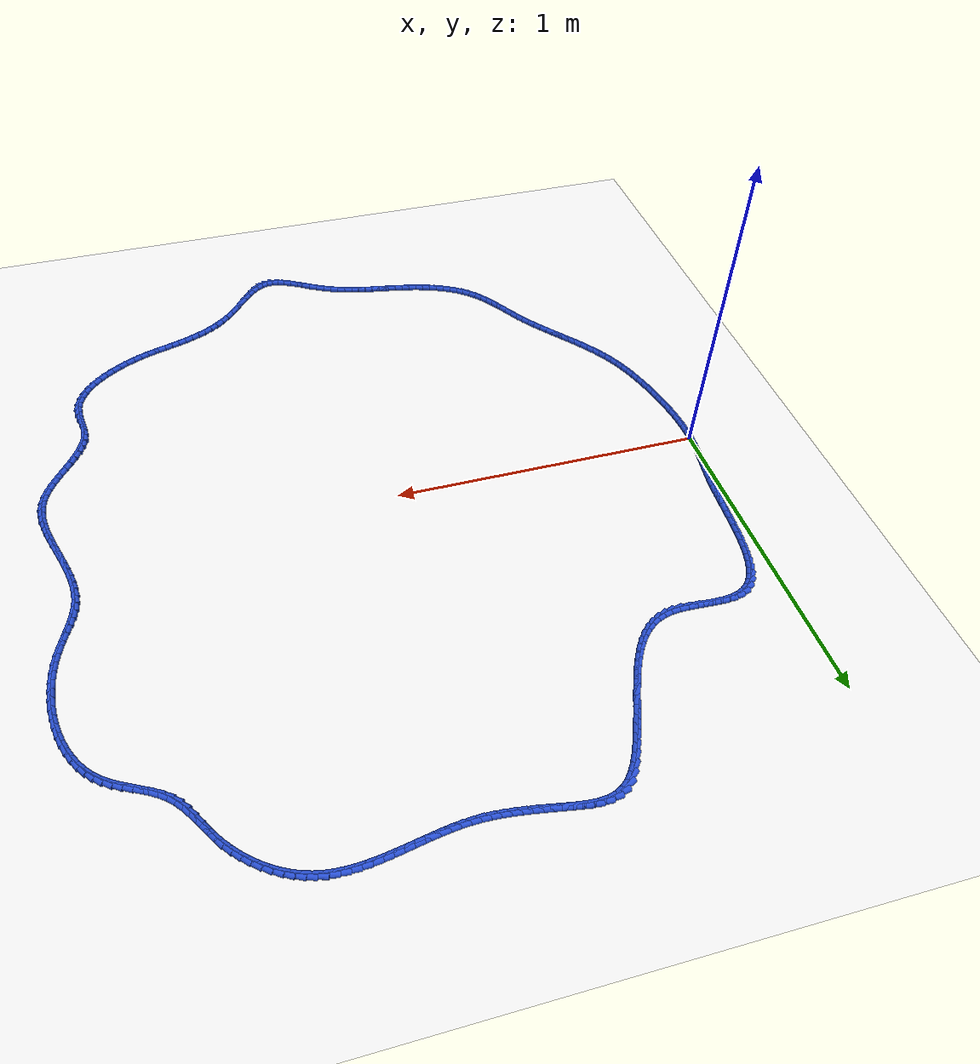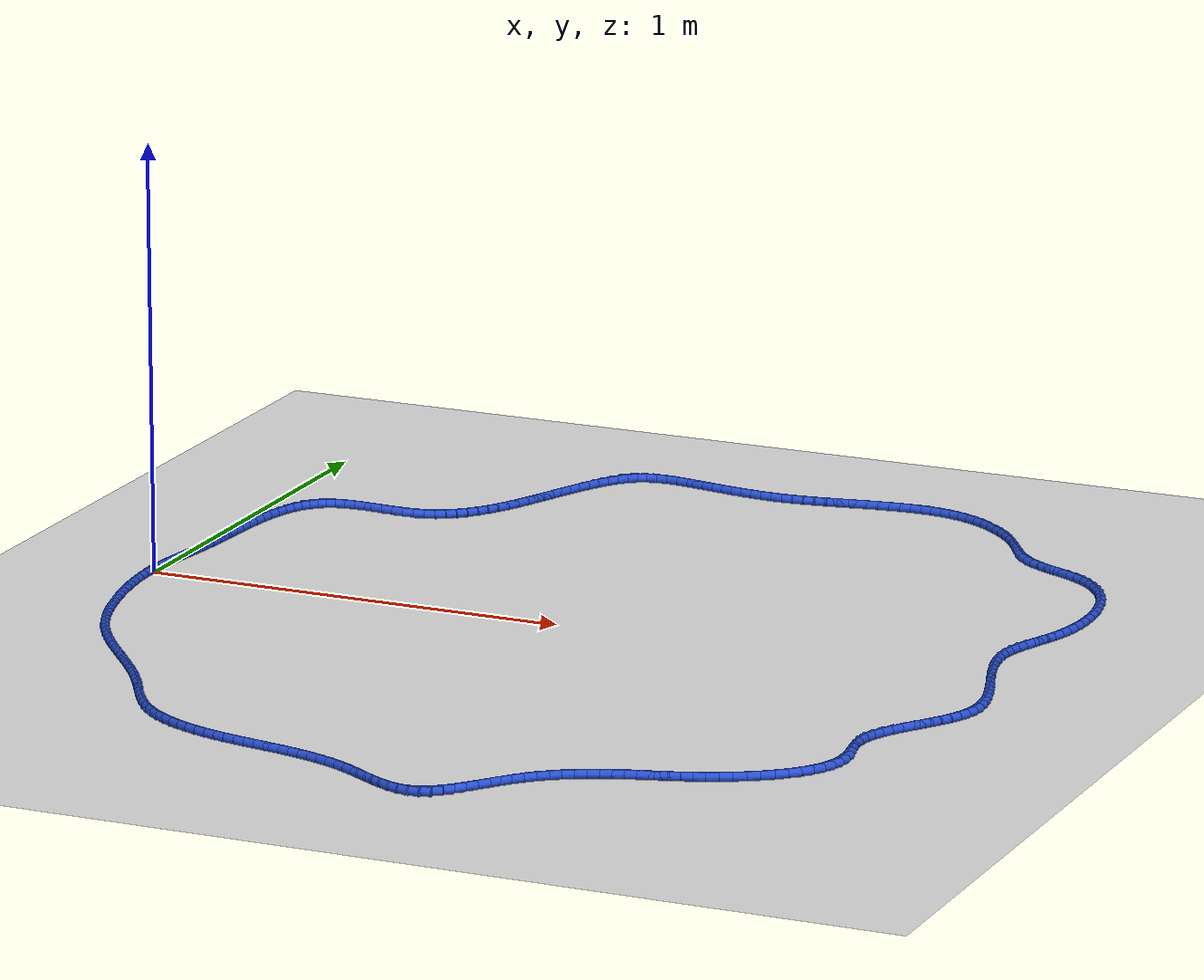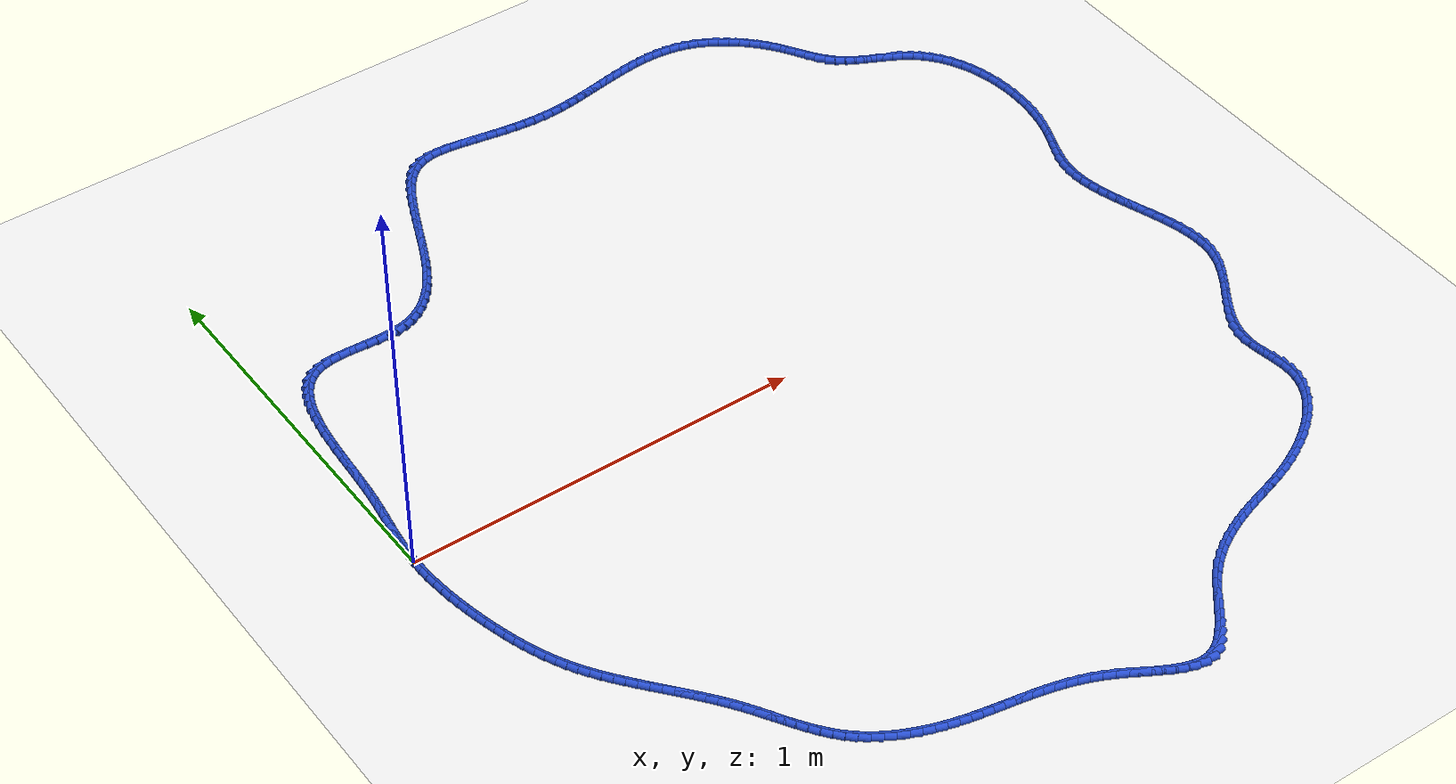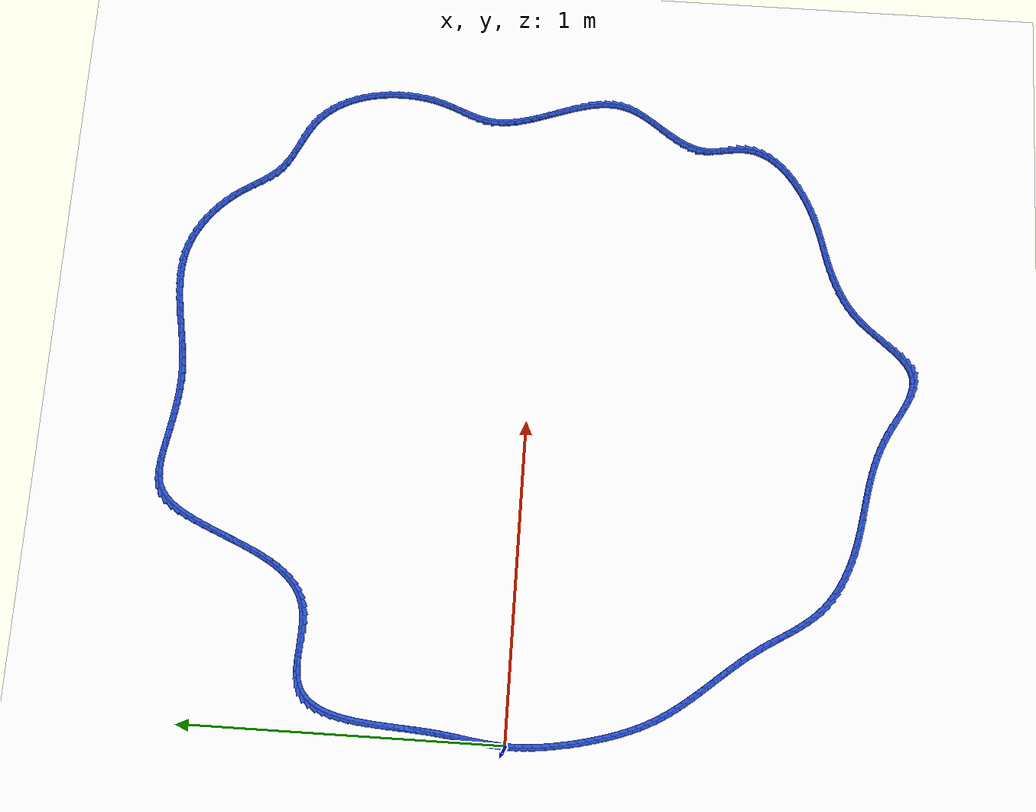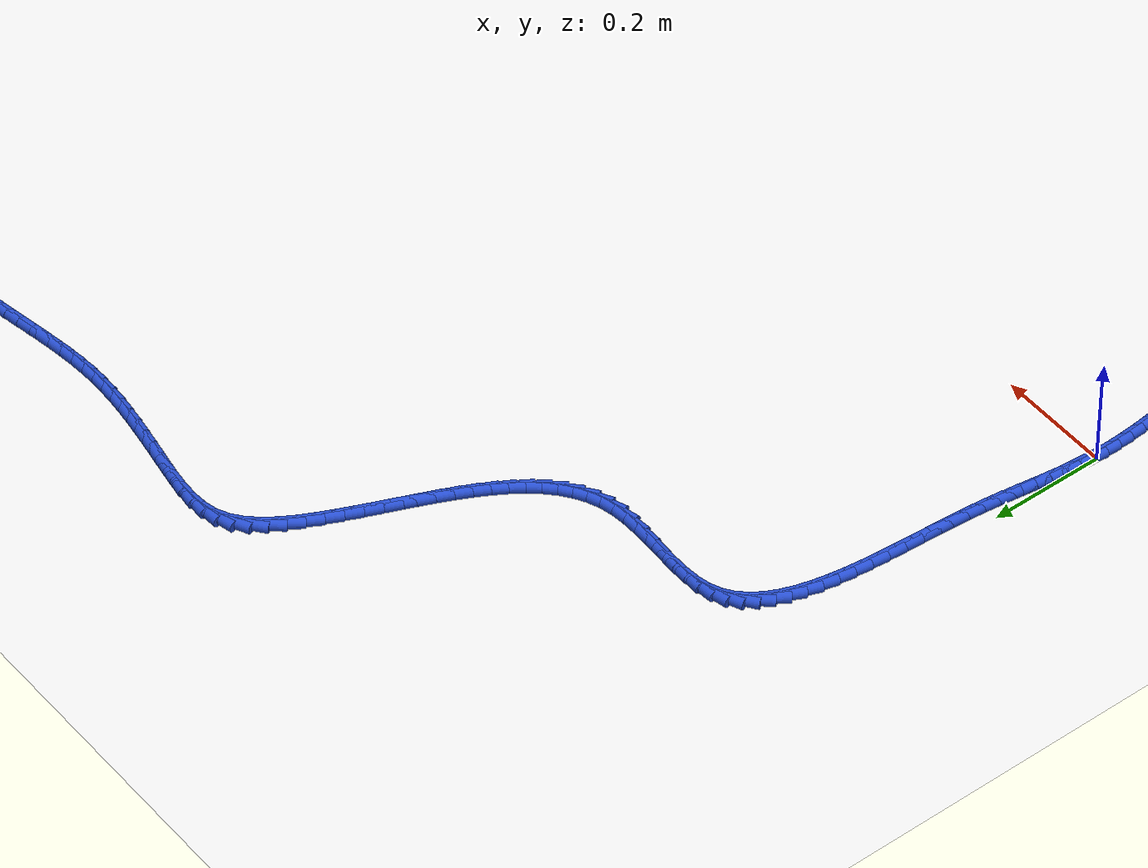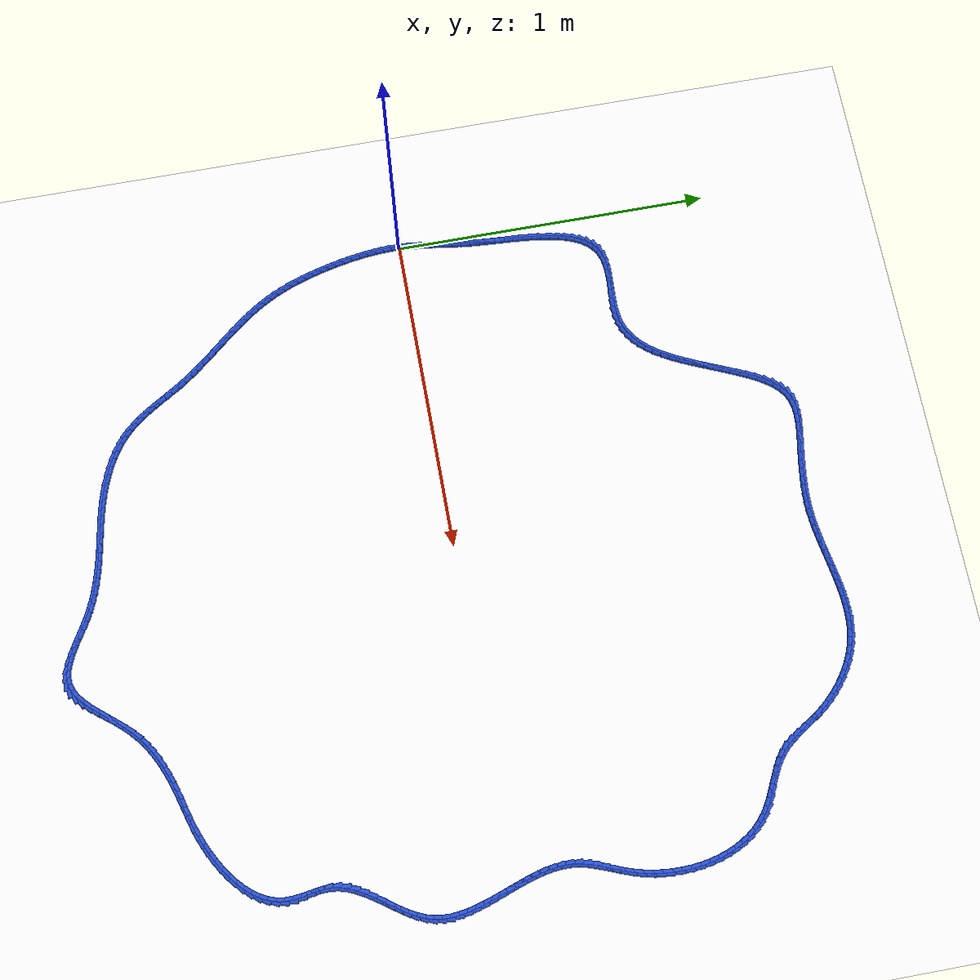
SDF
<sdf version="1.6">
 <world name="default">
  <light name="sun" type="directional">
   <pose>0 0 10 0 -0 0</pose>
   <diffuse>0.8 0.8 0.8 1</diffuse>
   <specular>0.2 0.2 0.2 1</specular>
   <attenuation>
    <range>1000</range>
    <constant>0.9</constant>
    <linear>0.01</linear>
    <quadratic>0.001</quadratic>
   </attenuation>
   <direction>-0.5 0.1 -0.9</direction>
  </light>
  <model name="ground_plane">
   <static>1</static>
   <link name="link">
    <collision name="collision">
     <geometry><plane><normal>0 0 1</normal><size>100 100</size></plane></geometry>
     <surface><friction><ode><mu>100</mu><mu2>50</mu2></ode></friction></surface>
    </collision>
    <visual name="visual">
     <cast_shadows>0</cast_shadows>
     <geometry><plane><normal>0 0 1</normal><size>100 100</size></plane></geometry>
     <material>
      <script><uri>file://media/materials/scripts/gazebo.material</uri><name>Gazebo/WhiteGlow</name></script>
     </material>
    </visual>
   </link>
  </model>
  <gravity>0 0 -9.8</gravity>
  <magnetic_field>6e-06 2.3e-05 -4.2e-05</magnetic_field>
  <atmosphere type="adiabatic"/>
  <physics name="default_physics" default="0" type="ode">
   <max_step_size>0.001</max_step_size>
   <real_time_factor>1</real_time_factor>
   <real_time_update_rate>1000</real_time_update_rate>
  </physics>
  <scene><ambient>0.4 0.4 0.4 1</ambient><background>0.7 0.7 0.7 1</background><shadows>1</shadows></scene>
  <spherical_coordinates>
   <surface_model>EARTH_WGS84</surface_model>
   <latitude_deg>0</latitude_deg>
   <longitude_deg>0</longitude_deg>
   <elevation>0</elevation>
   <heading_deg>0</heading_deg>
  </spherical_coordinates>
  <model name="line">
   <link name="link_0">
    <pose>-2.6020852139652106e-18 -6.938893903907228e-18 0.01 0 1.57 1.518536319305877</pose>
    <collision name="collision">
     <geometry><cylinder><radius>0.01</radius><length>0.08</length></cylinder></geometry>
    </collision>
    <visual name="visual">
     <material>
      <script><name>Gazebo/Blue</name><uri>file://media/materials/scripts/gazebo.material</uri></script>
     </material>
     <geometry><cylinder><radius>0.01</radius><length>0.08</length></cylinder></geometry>
    </visual>
   </link>
   <link name="link_1">
    <pose>0.0013273431235054972 0.025375704951247566 0.01 0 1.57 1.4831038697782482</pose>
    <collision name="collision">
     <geometry><cylinder><radius>0.01</radius><length>0.08</length></cylinder></geometry>
    </collision>
    <visual name="visual">
     <material>
      <script><name>Gazebo/Blue</name><uri>file://media/materials/scripts/gazebo.material</uri></script>
     </material>
     <geometry><cylinder><radius>0.01</radius><length>0.08</length></cylinder></geometry>
    </visual>
   </link>
   <link name="link_2">
    <pose>0.003543218310889586 0.05057960898288051 0.01 0 1.57 1.4558953160932735</pose>
    <collision name="collision">
     <geometry><cylinder><radius>0.01</radius><length>0.08</length></cylinder></geometry>
    </collision>
    <visual name="visual">
     <material>
      <script><name>Gazebo/Blue</name><uri>file://media/materials/scripts/gazebo.material</uri></script>
     </material>
     <geometry><cylinder><radius>0.01</radius><length>0.08</length></cylinder></geometry>
    </visual>
   </link>
   <link name="link_3">
    <pose>0.006453111025996179 0.07579327515895934 0.01 0 1.57 1.4373915896565748</pose>
    <collision name="collision">
     <geometry><cylinder><radius>0.01</radius><length>0.08</length></cylinder></geometry>
    </collision>
    <visual name="visual">
     <material>
      <script><name>Gazebo/Blue</name><uri>file://media/materials/scripts/gazebo.material</uri></script>
     </material>
     <geometry><cylinder><radius>0.01</radius><length>0.08</length></cylinder></geometry>
    </visual>
   </link>
   <link name="link_4">
    <pose>0.009862506732669196 0.1011982665435445 0.01 0 1.57 1.4276894007576038</pose>
    <collision name="collision">
     <geometry><cylinder><radius>0.01</radius><length>0.08</length></cylinder></geometry>
    </collision>
    <visual name="visual">
     <material>
      <script><name>Gazebo/Blue</name><uri>file://media/materials/scripts/gazebo.material</uri></script>
     </material>
     <geometry><cylinder><radius>0.01</radius><length>0.08</length></cylinder></geometry>
    </visual>
   </link>
   <link name="link_5">
    <pose>0.013576890894752551 0.1269761462006965 0.01 0 1.57 1.4265518259724992</pose>
    <collision name="collision">
     <geometry><cylinder><radius>0.01</radius><length>0.08</length></cylinder></geometry>
    </collision>
    <visual name="visual">
     <material>
      <script><name>Gazebo/Blue</name><uri>file://media/materials/scripts/gazebo.material</uri></script>
     </material>
     <geometry><cylinder><radius>0.01</radius><length>0.08</length></cylinder></geometry>
    </visual>
   </link>
   <link name="link_6">
    <pose>0.01740174897609017 0.15330847719447588 0.01 0 1.57 1.4334672283953678</pose>
    <collision name="collision">
     <geometry><cylinder><radius>0.01</radius><length>0.08</length></cylinder></geometry>
    </collision>
    <visual name="visual">
     <material>
      <script><name>Gazebo/Blue</name><uri>file://media/materials/scripts/gazebo.material</uri></script>
     </material>
     <geometry><cylinder><radius>0.01</radius><length>0.08</length></cylinder></geometry>
    </visual>
   </link>
   <link name="link_7">
    <pose>0.021142566440525958 0.1803768225889431 0.01 0 1.57 1.447707330328703</pose>
    <collision name="collision">
     <geometry><cylinder><radius>0.01</radius><length>0.08</length></cylinder></geometry>
    </collision>
    <visual name="visual">
     <material>
      <script><name>Gazebo/Blue</name><uri>file://media/materials/scripts/gazebo.material</uri></script>
     </material>
     <geometry><cylinder><radius>0.01</radius><length>0.08</length></cylinder></geometry>
    </visual>
   </link>
   <link name="link_8">
    <pose>0.02460482875190385 0.20836274544815864 0.01 0 1.57 1.4683490416714402</pose>
    <collision name="collision">
     <geometry><cylinder><radius>0.01</radius><length>0.08</length></cylinder></geometry>
    </collision>
    <visual name="visual">
     <material>
      <script><name>Gazebo/Blue</name><uri>file://media/materials/scripts/gazebo.material</uri></script>
     </material>
     <geometry><cylinder><radius>0.01</radius><length>0.08</length></cylinder></geometry>
    </visual>
   </link>
   <link name="link_9">
    <pose>0.027594875719136228 0.23744676667266695 0.01 0 1.57 1.489880821835114</pose>
    <collision name="collision">
     <geometry><cylinder><radius>0.01</radius><length>0.08</length></cylinder></geometry>
    </collision>
    <visual name="visual">
     <material>
      <script><name>Gazebo/Blue</name><uri>file://media/materials/scripts/gazebo.material</uri></script>
     </material>
     <geometry><cylinder><radius>0.01</radius><length>0.08</length></cylinder></geometry>
    </visual>
   </link>
   <link name="link_10">
    <pose>0.030044636717430816 0.2676562080999955 0.01 0 1.57 1.5033187484475186</pose>
    <collision name="collision">
     <geometry><cylinder><radius>0.01</radius><length>0.08</length></cylinder></geometry>
    </collision>
    <visual name="visual">
     <material>
      <script><name>Gazebo/Blue</name><uri>file://media/materials/scripts/gazebo.material</uri></script>
     </material>
     <geometry><cylinder><radius>0.01</radius><length>0.08</length></cylinder></geometry>
    </visual>
   </link>
   <link name="link_11">
    <pose>0.032142922190807964 0.29870503799691056 0.01 0 1.57 1.5085578318496928</pose>
    <collision name="collision">
     <geometry><cylinder><radius>0.01</radius><length>0.08</length></cylinder></geometry>
    </collision>
    <visual name="visual">
     <material>
      <script><name>Gazebo/Blue</name><uri>file://media/materials/scripts/gazebo.material</uri></script>
     </material>
     <geometry><cylinder><radius>0.01</radius><length>0.08</length></cylinder></geometry>
    </visual>
   </link>
   <link name="link_12">
    <pose>0.03410995069347177 0.3302689117894446 0.01 0 1.57 1.5061403062061889</pose>
    <collision name="collision">
     <geometry><cylinder><radius>0.01</radius><length>0.08</length></cylinder></geometry>
    </collision>
    <visual name="visual">
     <material>
      <script><name>Gazebo/Blue</name><uri>file://media/materials/scripts/gazebo.material</uri></script>
     </material>
     <geometry><cylinder><radius>0.01</radius><length>0.08</length></cylinder></geometry>
    </visual>
   </link>
   <link name="link_13">
    <pose>0.03616594077962635 0.3620234849036305 0.01 0 1.57 1.4961377276590273</pose>
    <collision name="collision">
     <geometry><cylinder><radius>0.01</radius><length>0.08</length></cylinder></geometry>
    </collision>
    <visual name="visual">
     <material>
      <script><name>Gazebo/Blue</name><uri>file://media/materials/scripts/gazebo.material</uri></script>
     </material>
     <geometry><cylinder><radius>0.01</radius><length>0.08</length></cylinder></geometry>
    </visual>
   </link>
   <link name="link_14">
    <pose>0.03853111100347581 0.3936444127655007 0.01 0 1.57 1.4781770966286956</pose>
    <collision name="collision">
     <geometry><cylinder><radius>0.01</radius><length>0.08</length></cylinder></geometry>
    </collision>
    <visual name="visual">
     <material>
      <script><name>Gazebo/Blue</name><uri>file://media/materials/scripts/gazebo.material</uri></script>
     </material>
     <geometry><cylinder><radius>0.01</radius><length>0.08</length></cylinder></geometry>
    </visual>
   </link>
   <link name="link_15">
    <pose>0.04142567991922423 0.4248073508010879 0.01 0 1.57 1.4514156284007513</pose>
    <collision name="collision">
     <geometry><cylinder><radius>0.01</radius><length>0.08</length></cylinder></geometry>
    </collision>
    <visual name="visual">
     <material>
      <script><name>Gazebo/Blue</name><uri>file://media/materials/scripts/gazebo.material</uri></script>
     </material>
     <geometry><cylinder><radius>0.01</radius><length>0.08</length></cylinder></geometry>
    </visual>
   </link>
   <link name="link_16">
    <pose>0.045069866081075736 0.4551879544364248 0.01 0 1.57 1.4144669831270131</pose>
    <collision name="collision">
     <geometry><cylinder><radius>0.01</radius><length>0.08</length></cylinder></geometry>
    </collision>
    <visual name="visual">
     <material>
      <script><name>Gazebo/Blue</name><uri>file://media/materials/scripts/gazebo.material</uri></script>
     </material>
     <geometry><cylinder><radius>0.01</radius><length>0.08</length></cylinder></geometry>
    </visual>
   </link>
   <link name="link_17">
    <pose>0.04968388804323444 0.48446187909754396 0.01 0 1.57 1.3652814309231334</pose>
    <collision name="collision">
     <geometry><cylinder><radius>0.01</radius><length>0.08</length></cylinder></geometry>
    </collision>
    <visual name="visual">
     <material>
      <script><name>Gazebo/Blue</name><uri>file://media/materials/scripts/gazebo.material</uri></script>
     </material>
     <geometry><cylinder><radius>0.01</radius><length>0.08</length></cylinder></geometry>
    </visual>
   </link>
   <link name="link_18">
    <pose>0.0554879643599044 0.5123047802104779 0.01 0 1.57 1.300995292122116</pose>
    <collision name="collision">
     <geometry><cylinder><radius>0.01</radius><length>0.08</length></cylinder></geometry>
    </collision>
    <visual name="visual">
     <material>
      <script><name>Gazebo/Blue</name><uri>file://media/materials/scripts/gazebo.material</uri></script>
     </material>
     <geometry><cylinder><radius>0.01</radius><length>0.08</length></cylinder></geometry>
    </visual>
   </link>
   <link name="link_19">
    <pose>0.0627023135852898 0.5383923132012595 0.01 0 1.57 1.217811283853974</pose>
    <collision name="collision">
     <geometry><cylinder><radius>0.01</radius><length>0.08</length></cylinder></geometry>
    </collision>
    <visual name="visual">
     <material>
      <script><name>Gazebo/Blue</name><uri>file://media/materials/scripts/gazebo.material</uri></script>
     </material>
     <geometry><cylinder><radius>0.01</radius><length>0.08</length></cylinder></geometry>
    </visual>
   </link>
   <link name="link_20">
    <pose>0.07154715427359462 0.562400133495921 0.01 0 1.57 1.111093956603589</pose>
    <collision name="collision">
     <geometry><cylinder><radius>0.01</radius><length>0.08</length></cylinder></geometry>
    </collision>
    <visual name="visual">
     <material>
      <script><name>Gazebo/Blue</name><uri>file://media/materials/scripts/gazebo.material</uri></script>
     </material>
     <geometry><cylinder><radius>0.01</radius><length>0.08</length></cylinder></geometry>
    </visual>
   </link>
   <link name="link_21">
    <pose>0.08224270497902311 0.5840038965204956 0.01 0 1.57 0.9761151240698267</pose>
    <collision name="collision">
     <geometry><cylinder><radius>0.01</radius><length>0.08</length></cylinder></geometry>
    </collision>
    <visual name="visual">
     <material>
      <script><name>Gazebo/Blue</name><uri>file://media/materials/scripts/gazebo.material</uri></script>
     </material>
     <geometry><cylinder><radius>0.01</radius><length>0.08</length></cylinder></geometry>
    </visual>
   </link>
   <link name="link_22">
    <pose>0.09500918425577928 0.6028792577010152 0.01 0 1.57 0.810165843333273</pose>
    <collision name="collision">
     <geometry><cylinder><radius>0.01</radius><length>0.08</length></cylinder></geometry>
    </collision>
    <visual name="visual">
     <material>
      <script><name>Gazebo/Blue</name><uri>file://media/materials/scripts/gazebo.material</uri></script>
     </material>
     <geometry><cylinder><radius>0.01</radius><length>0.08</length></cylinder></geometry>
    </visual>
   </link>
   <link name="link_23">
    <pose>0.11006681065806723 0.6187018724635133 0.01 0 1.57 0.6163280557996347</pose>
    <collision name="collision">
     <geometry><cylinder><radius>0.01</radius><length>0.08</length></cylinder></geometry>
    </collision>
    <visual name="visual">
     <material>
      <script><name>Gazebo/Blue</name><uri>file://media/materials/scripts/gazebo.material</uri></script>
     </material>
     <geometry><cylinder><radius>0.01</radius><length>0.08</length></cylinder></geometry>
    </visual>
   </link>
   <link name="link_24">
    <pose>0.1276358027400911 0.6311473962340217 0.01 0 1.57 0.4068288492646526</pose>
    <collision name="collision">
     <geometry><cylinder><radius>0.01</radius><length>0.08</length></cylinder></geometry>
    </collision>
    <visual name="visual">
     <material>
      <script><name>Gazebo/Blue</name><uri>file://media/materials/scripts/gazebo.material</uri></script>
     </material>
     <geometry><cylinder><radius>0.01</radius><length>0.08</length></cylinder></geometry>
    </visual>
   </link>
   <link name="link_25">
    <pose>0.147934940979745 0.6398936085173469 0.01 0 1.57 0.21703779530122946</pose>
    <collision name="collision">
     <geometry><cylinder><radius>0.01</radius><length>0.08</length></cylinder></geometry>
    </collision>
    <visual name="visual">
     <material>
      <script><name>Gazebo/Blue</name><uri>file://media/materials/scripts/gazebo.material</uri></script>
     </material>
     <geometry><cylinder><radius>0.01</radius><length>0.08</length></cylinder></geometry>
    </visual>
   </link>
   <link name="link_26">
    <pose>0.1709463238221766 0.644967874774373 0.01 0 1.57 0.08568359429457617</pose>
    <collision name="collision">
     <geometry><cylinder><radius>0.01</radius><length>0.08</length></cylinder></geometry>
    </collision>
    <visual name="visual">
     <material>
      <script><name>Gazebo/Blue</name><uri>file://media/materials/scripts/gazebo.material</uri></script>
     </material>
     <geometry><cylinder><radius>0.01</radius><length>0.08</length></cylinder></geometry>
    </visual>
   </link>
   <link name="link_27">
    <pose>0.19615408535262951 0.6471330676983266 0.01 0 1.57 0.004173853943164832</pose>
    <collision name="collision">
     <geometry><cylinder><radius>0.01</radius><length>0.08</length></cylinder></geometry>
    </collision>
    <visual name="visual">
     <material>
      <script><name>Gazebo/Blue</name><uri>file://media/materials/scripts/gazebo.material</uri></script>
     </material>
     <geometry><cylinder><radius>0.01</radius><length>0.08</length></cylinder></geometry>
    </visual>
   </link>
   <link name="link_28">
    <pose>0.22297941340466867 0.6472450333497807 0.01 0 1.57 -0.038934246516687934</pose>
    <collision name="collision">
     <geometry><cylinder><radius>0.01</radius><length>0.08</length></cylinder></geometry>
    </collision>
    <visual name="visual">
     <material>
      <script><name>Gazebo/Blue</name><uri>file://media/materials/scripts/gazebo.material</uri></script>
     </material>
     <geometry><cylinder><radius>0.01</radius><length>0.08</length></cylinder></geometry>
    </visual>
   </link>
   <link name="link_29">
    <pose>0.2508434958118586 0.646159617789307 0.01 0 1.57 -0.05033696028064199</pose>
    <collision name="collision">
     <geometry><cylinder><radius>0.01</radius><length>0.08</length></cylinder></geometry>
    </collision>
    <visual name="visual">
     <material>
      <script><name>Gazebo/Blue</name><uri>file://media/materials/scripts/gazebo.material</uri></script>
     </material>
     <geometry><cylinder><radius>0.01</radius><length>0.08</length></cylinder></geometry>
    </visual>
   </link>
   <link name="link_30">
    <pose>0.2791675204077644 0.6447326670774781 0.01 0 1.57 -0.03234591361597923</pose>
    <collision name="collision">
     <geometry><cylinder><radius>0.01</radius><length>0.08</length></cylinder></geometry>
    </collision>
    <visual name="visual">
     <material>
      <script><name>Gazebo/Blue</name><uri>file://media/materials/scripts/gazebo.material</uri></script>
     </material>
     <geometry><cylinder><radius>0.01</radius><length>0.08</length></cylinder></geometry>
    </visual>
   </link>
   <link name="link_31">
    <pose>0.3073726750259505 0.6438200272748664 0.01 0 1.57 0.016630934942488275</pose>
    <collision name="collision">
     <geometry><cylinder><radius>0.01</radius><length>0.08</length></cylinder></geometry>
    </collision>
    <visual name="visual">
     <material>
      <script><name>Gazebo/Blue</name><uri>file://media/materials/scripts/gazebo.material</uri></script>
     </material>
     <geometry><cylinder><radius>0.01</radius><length>0.08</length></cylinder></geometry>
    </visual>
   </link>
   <link name="link_32">
    <pose>0.3348801474999821 0.6442775444420444 0.01 0 1.57 0.10194879602931628</pose>
    <collision name="collision">
     <geometry><cylinder><radius>0.01</radius><length>0.08</length></cylinder></geometry>
    </collision>
    <visual name="visual">
     <material>
      <script><name>Gazebo/Blue</name><uri>file://media/materials/scripts/gazebo.material</uri></script>
     </material>
     <geometry><cylinder><radius>0.01</radius><length>0.08</length></cylinder></geometry>
    </visual>
   </link>
   <link name="link_33">
    <pose>0.3611111256634238 0.6469610646395844 0.01 0 1.57 0.22973171142016255</pose>
    <collision name="collision">
     <geometry><cylinder><radius>0.01</radius><length>0.08</length></cylinder></geometry>
    </collision>
    <visual name="visual">
     <material>
      <script><name>Gazebo/Blue</name><uri>file://media/materials/scripts/gazebo.material</uri></script>
     </material>
     <geometry><cylinder><radius>0.01</radius><length>0.08</length></cylinder></geometry>
    </visual>
   </link>
   <link name="link_34">
    <pose>0.38552446452016487 0.6526703774179967 0.01 0 1.57 0.37688570544076144</pose>
    <collision name="collision">
     <geometry><cylinder><radius>0.01</radius><length>0.08</length></cylinder></geometry>
    </collision>
    <visual name="visual">
     <material>
      <script><name>Gazebo/Blue</name><uri>file://media/materials/scripts/gazebo.material</uri></script>
     </material>
     <geometry><cylinder><radius>0.01</radius><length>0.08</length></cylinder></geometry>
    </visual>
   </link>
   <link name="link_35">
    <pose>0.4080066002983976 0.6615689433708777 0.01 0 1.57 0.5196748217189355</pose>
    <collision name="collision">
     <geometry><cylinder><radius>0.01</radius><length>0.08</length></cylinder></geometry>
    </collision>
    <visual name="visual">
     <material>
      <script><name>Gazebo/Blue</name><uri>file://media/materials/scripts/gazebo.material</uri></script>
     </material>
     <geometry><cylinder><radius>0.01</radius><length>0.08</length></cylinder></geometry>
    </visual>
   </link>
   <link name="link_36">
    <pose>0.42871501488762936 0.6734168513038742 0.01 0 1.57 0.6511174869187879</pose>
    <collision name="collision">
     <geometry><cylinder><radius>0.01</radius><length>0.08</length></cylinder></geometry>
    </collision>
    <visual name="visual">
     <material>
      <script><name>Gazebo/Blue</name><uri>file://media/materials/scripts/gazebo.material</uri></script>
     </material>
     <geometry><cylinder><radius>0.01</radius><length>0.08</length></cylinder></geometry>
    </visual>
   </link>
   <link name="link_37">
    <pose>0.4478114962008734 0.6879677817724799 0.01 0 1.57 0.7669693919560285</pose>
    <collision name="collision">
     <geometry><cylinder><radius>0.01</radius><length>0.08</length></cylinder></geometry>
    </collision>
    <visual name="visual">
     <material>
      <script><name>Gazebo/Blue</name><uri>file://media/materials/scripts/gazebo.material</uri></script>
     </material>
     <geometry><cylinder><radius>0.01</radius><length>0.08</length></cylinder></geometry>
    </visual>
   </link>
   <link name="link_38">
    <pose>0.4654578321511435 0.7049754153321884 0.01 0 1.57 0.8656180144133736</pose>
    <collision name="collision">
     <geometry><cylinder><radius>0.01</radius><length>0.08</length></cylinder></geometry>
    </collision>
    <visual name="visual">
     <material>
      <script><name>Gazebo/Blue</name><uri>file://media/materials/scripts/gazebo.material</uri></script>
     </material>
     <geometry><cylinder><radius>0.01</radius><length>0.08</length></cylinder></geometry>
    </visual>
   </link>
   <link name="link_39">
    <pose>0.48181581065145324 0.7241934325384934 0.01 0 1.57 0.9473857293996624</pose>
    <collision name="collision">
     <geometry><cylinder><radius>0.01</radius><length>0.08</length></cylinder></geometry>
    </collision>
    <visual name="visual">
     <material>
      <script><name>Gazebo/Blue</name><uri>file://media/materials/scripts/gazebo.material</uri></script>
     </material>
     <geometry><cylinder><radius>0.01</radius><length>0.08</length></cylinder></geometry>
    </visual>
   </link>
   <link name="link_40">
    <pose>0.49704721961481596 0.7453755139468878 0.01 0 1.57 1.013635385515416</pose>
    <collision name="collision">
     <geometry><cylinder><radius>0.01</radius><length>0.08</length></cylinder></geometry>
    </collision>
    <visual name="visual">
     <material>
      <script><name>Gazebo/Blue</name><uri>file://media/materials/scripts/gazebo.material</uri></script>
     </material>
     <geometry><cylinder><radius>0.01</radius><length>0.08</length></cylinder></geometry>
    </visual>
   </link>
   <link name="link_41">
    <pose>0.5113138469542453 0.7682753401128655 0.01 0 1.57 1.0660823713414747</pose>
    <collision name="collision">
     <geometry><cylinder><radius>0.01</radius><length>0.08</length></cylinder></geometry>
    </collision>
    <visual name="visual">
     <material>
      <script><name>Gazebo/Blue</name><uri>file://media/materials/scripts/gazebo.material</uri></script>
     </material>
     <geometry><cylinder><radius>0.01</radius><length>0.08</length></cylinder></geometry>
    </visual>
   </link>
   <link name="link_42">
    <pose>0.5247774805827551 0.7926465915919201 0.01 0 1.57 1.1063911110405942</pose>
    <collision name="collision">
     <geometry><cylinder><radius>0.01</radius><length>0.08</length></cylinder></geometry>
    </collision>
    <visual name="visual">
     <material>
      <script><name>Gazebo/Blue</name><uri>file://media/materials/scripts/gazebo.material</uri></script>
     </material>
     <geometry><cylinder><radius>0.01</radius><length>0.08</length></cylinder></geometry>
    </visual>
   </link>
   <link name="link_43">
    <pose>0.5375999084133589 0.8182429489395453 0.01 0 1.57 1.135985259736726</pose>
    <collision name="collision">
     <geometry><cylinder><radius>0.01</radius><length>0.08</length></cylinder></geometry>
    </collision>
    <visual name="visual">
     <material>
      <script><name>Gazebo/Blue</name><uri>file://media/materials/scripts/gazebo.material</uri></script>
     </material>
     <geometry><cylinder><radius>0.01</radius><length>0.08</length></cylinder></geometry>
    </visual>
   </link>
   <link name="link_44">
    <pose>0.5499429183590699 0.8448180927112341 0.01 0 1.57 1.1559817338353384</pose>
    <collision name="collision">
     <geometry><cylinder><radius>0.01</radius><length>0.08</length></cylinder></geometry>
    </collision>
    <visual name="visual">
     <material>
      <script><name>Gazebo/Blue</name><uri>file://media/materials/scripts/gazebo.material</uri></script>
     </material>
     <geometry><cylinder><radius>0.01</radius><length>0.08</length></cylinder></geometry>
    </visual>
   </link>
   <link name="link_45">
    <pose>0.5619682983329021 0.8721257034624803 0.01 0 1.57 1.167184098190263</pose>
    <collision name="collision">
     <geometry><cylinder><radius>0.01</radius><length>0.08</length></cylinder></geometry>
    </collision>
    <visual name="visual">
     <material>
      <script><name>Gazebo/Blue</name><uri>file://media/materials/scripts/gazebo.material</uri></script>
     </material>
     <geometry><cylinder><radius>0.01</radius><length>0.08</length></cylinder></geometry>
    </visual>
   </link>
   <link name="link_46">
    <pose>0.5738378362478687 0.8999194617487771 0.01 0 1.57 1.17009828035698</pose>
    <collision name="collision">
     <geometry><cylinder><radius>0.01</radius><length>0.08</length></cylinder></geometry>
    </collision>
    <visual name="visual">
     <material>
      <script><name>Gazebo/Blue</name><uri>file://media/materials/scripts/gazebo.material</uri></script>
     </material>
     <geometry><cylinder><radius>0.01</radius><length>0.08</length></cylinder></geometry>
    </visual>
   </link>
   <link name="link_47">
    <pose>0.5857133200169835 0.9279530481256186 0.01 0 1.57 1.1649522408020414</pose>
    <collision name="collision">
     <geometry><cylinder><radius>0.01</radius><length>0.08</length></cylinder></geometry>
    </collision>
    <visual name="visual">
     <material>
      <script><name>Gazebo/Blue</name><uri>file://media/materials/scripts/gazebo.material</uri></script>
     </material>
     <geometry><cylinder><radius>0.01</radius><length>0.08</length></cylinder></geometry>
    </visual>
   </link>
   <link name="link_48">
    <pose>0.5977565375532603 0.955980143148498 0.01 0 1.57 1.1517120613173357</pose>
    <collision name="collision">
     <geometry><cylinder><radius>0.01</radius><length>0.08</length></cylinder></geometry>
    </collision>
    <visual name="visual">
     <material>
      <script><name>Gazebo/Blue</name><uri>file://media/materials/scripts/gazebo.material</uri></script>
     </material>
     <geometry><cylinder><radius>0.01</radius><length>0.08</length></cylinder></geometry>
    </visual>
   </link>
   <link name="link_49">
    <pose>0.6101292767697122 0.9837544273729087 0.01 0 1.57 1.1300278328495221</pose>
    <collision name="collision">
     <geometry><cylinder><radius>0.01</radius><length>0.08</length></cylinder></geometry>
    </collision>
    <visual name="visual">
     <material>
      <script><name>Gazebo/Blue</name><uri>file://media/materials/scripts/gazebo.material</uri></script>
     </material>
     <geometry><cylinder><radius>0.01</radius><length>0.08</length></cylinder></geometry>
    </visual>
   </link>
   <link name="link_50">
    <pose>0.6229941832206943 1.011026781777434 0.01 0 1.57 1.0948579477988312</pose>
    <collision name="collision">
     <geometry><cylinder><radius>0.01</radius><length>0.08</length></cylinder></geometry>
    </collision>
    <visual name="visual">
     <material>
      <script><name>Gazebo/Blue</name><uri>file://media/materials/scripts/gazebo.material</uri></script>
     </material>
     <geometry><cylinder><radius>0.01</radius><length>0.08</length></cylinder></geometry>
    </visual>
   </link>
   <link name="link_51">
    <pose>0.6365701661014206 1.0373644273626608 0.01 0 1.57 1.036645545284551</pose>
    <collision name="collision">
     <geometry><cylinder><radius>0.01</radius><length>0.08</length></cylinder></geometry>
    </collision>
    <visual name="visual">
     <material>
      <script><name>Gazebo/Blue</name><uri>file://media/materials/scripts/gazebo.material</uri></script>
     </material>
     <geometry><cylinder><radius>0.01</radius><length>0.08</length></cylinder></geometry>
    </visual>
   </link>
   <link name="link_52">
    <pose>0.651166224523165 1.0620405068976824 0.01 0 1.57 0.9495851570418905</pose>
    <collision name="collision">
     <geometry><cylinder><radius>0.01</radius><length>0.08</length></cylinder></geometry>
    </collision>
    <visual name="visual">
     <material>
      <script><name>Gazebo/Blue</name><uri>file://media/materials/scripts/gazebo.material</uri></script>
     </material>
     <geometry><cylinder><radius>0.01</radius><length>0.08</length></cylinder></geometry>
    </visual>
   </link>
   <link name="link_53">
    <pose>0.6670994540881329 1.084301733981288 0.01 0 1.57 0.82642115321409</pose>
    <collision name="collision">
     <geometry><cylinder><radius>0.01</radius><length>0.08</length></cylinder></geometry>
    </collision>
    <visual name="visual">
     <material>
      <script><name>Gazebo/Blue</name><uri>file://media/materials/scripts/gazebo.material</uri></script>
     </material>
     <geometry><cylinder><radius>0.01</radius><length>0.08</length></cylinder></geometry>
    </visual>
   </link>
   <link name="link_54">
    <pose>0.6846869503985293 1.1033948222122654 0.01 0 1.57 0.6597426627919771</pose>
    <collision name="collision">
     <geometry><cylinder><radius>0.01</radius><length>0.08</length></cylinder></geometry>
    </collision>
    <visual name="visual">
     <material>
      <script><name>Gazebo/Blue</name><uri>file://media/materials/scripts/gazebo.material</uri></script>
     </material>
     <geometry><cylinder><radius>0.01</radius><length>0.08</length></cylinder></geometry>
    </visual>
   </link>
   <link name="link_55">
    <pose>0.7042458090565595 1.1185664851894042 0.01 0 1.57 0.44811022827380975</pose>
    <collision name="collision">
     <geometry><cylinder><radius>0.01</radius><length>0.08</length></cylinder></geometry>
    </collision>
    <visual name="visual">
     <material>
      <script><name>Gazebo/Blue</name><uri>file://media/materials/scripts/gazebo.material</uri></script>
     </material>
     <geometry><cylinder><radius>0.01</radius><length>0.08</length></cylinder></geometry>
    </visual>
   </link>
   <link name="link_56">
    <pose>0.7260908041533228 1.1290679522054774 0.01 0 1.57 0.22888808641540567</pose>
    <collision name="collision">
     <geometry><cylinder><radius>0.01</radius><length>0.08</length></cylinder></geometry>
    </collision>
    <visual name="visual">
     <material>
      <script><name>Gazebo/Blue</name><uri>file://media/materials/scripts/gazebo.material</uri></script>
     </material>
     <geometry><cylinder><radius>0.01</radius><length>0.08</length></cylinder></geometry>
    </visual>
   </link>
   <link name="link_57">
    <pose>0.7502554210124772 1.1346976022058533 0.01 0 1.57 0.06226773911061828</pose>
    <collision name="collision">
     <geometry><cylinder><radius>0.01</radius><length>0.08</length></cylinder></geometry>
    </collision>
    <visual name="visual">
     <material>
      <script><name>Gazebo/Blue</name><uri>file://media/materials/scripts/gazebo.material</uri></script>
     </material>
     <geometry><cylinder><radius>0.01</radius><length>0.08</length></cylinder></geometry>
    </visual>
   </link>
   <link name="link_58">
    <pose>0.7762266326340874 1.1363168641492825 0.01 0 1.57 -0.05169660642214146</pose>
    <collision name="collision">
     <geometry><cylinder><radius>0.01</radius><length>0.08</length></cylinder></geometry>
    </collision>
    <visual name="visual">
     <material>
      <script><name>Gazebo/Blue</name><uri>file://media/materials/scripts/gazebo.material</uri></script>
     </material>
     <geometry><cylinder><radius>0.01</radius><length>0.08</length></cylinder></geometry>
    </visual>
   </link>
   <link name="link_59">
    <pose>0.8034285922448126 1.1349093610568948 0.01 0 1.57 -0.12324278193667765</pose>
    <collision name="collision">
     <geometry><cylinder><radius>0.01</radius><length>0.08</length></cylinder></geometry>
    </collision>
    <visual name="visual">
     <material>
      <script><name>Gazebo/Blue</name><uri>file://media/materials/scripts/gazebo.material</uri></script>
     </material>
     <geometry><cylinder><radius>0.01</radius><length>0.08</length></cylinder></geometry>
    </visual>
   </link>
   <link name="link_60">
    <pose>0.8312854530713119 1.1314587159498193 0.01 0 1.57 -0.1600656284863573</pose>
    <collision name="collision">
     <geometry><cylinder><radius>0.01</radius><length>0.08</length></cylinder></geometry>
    </collision>
    <visual name="visual">
     <material>
      <script><name>Gazebo/Blue</name><uri>file://media/materials/scripts/gazebo.material</uri></script>
     </material>
     <geometry><cylinder><radius>0.01</radius><length>0.08</length></cylinder></geometry>
    </visual>
   </link>
   <link name="link_61">
    <pose>0.8592213683402445 1.1269485518491849 0.01 0 1.57 -0.16826718416376282</pose>
    <collision name="collision">
     <geometry><cylinder><radius>0.01</radius><length>0.08</length></cylinder></geometry>
    </collision>
    <visual name="visual">
     <material>
      <script><name>Gazebo/Blue</name><uri>file://media/materials/scripts/gazebo.material</uri></script>
     </material>
     <geometry><cylinder><radius>0.01</radius><length>0.08</length></cylinder></geometry>
    </visual>
   </link>
   <link name="link_62">
    <pose>0.8867292380360123 1.122275694413723 0.01 0 1.57 -0.16457860910920244</pose>
    <collision name="collision">
     <geometry><cylinder><radius>0.01</radius><length>0.08</length></cylinder></geometry>
    </collision>
    <visual name="visual">
     <material>
      <script><name>Gazebo/Blue</name><uri>file://media/materials/scripts/gazebo.material</uri></script>
     </material>
     <geometry><cylinder><radius>0.01</radius><length>0.08</length></cylinder></geometry>
    </visual>
   </link>
   <link name="link_63">
    <pose>0.9137347034135185 1.1177906046136612 0.01 0 1.57 -0.15511378818893273</pose>
    <collision name="collision">
     <geometry><cylinder><radius>0.01</radius><length>0.08</length></cylinder></geometry>
    </collision>
    <visual name="visual">
     <material>
      <script><name>Gazebo/Blue</name><uri>file://media/materials/scripts/gazebo.material</uri></script>
     </material>
     <geometry><cylinder><radius>0.01</radius><length>0.08</length></cylinder></geometry>
    </visual>
   </link>
   <link name="link_64">
    <pose>0.9403313618412734 1.1136316876345143 0.01 0 1.57 -0.13966881673758877</pose>
    <collision name="collision">
     <geometry><cylinder><radius>0.01</radius><length>0.08</length></cylinder></geometry>
    </collision>
    <visual name="visual">
     <material>
      <script><name>Gazebo/Blue</name><uri>file://media/materials/scripts/gazebo.material</uri></script>
     </material>
     <geometry><cylinder><radius>0.01</radius><length>0.08</length></cylinder></geometry>
    </visual>
   </link>
   <link name="link_65">
    <pose>0.9666131816275629 1.1099368803256133 0.01 0 1.57 -0.11812168404609973</pose>
    <collision name="collision">
     <geometry><cylinder><radius>0.01</radius><length>0.08</length></cylinder></geometry>
    </collision>
    <visual name="visual">
     <material>
      <script><name>Gazebo/Blue</name><uri>file://media/materials/scripts/gazebo.material</uri></script>
     </material>
     <geometry><cylinder><radius>0.01</radius><length>0.08</length></cylinder></geometry>
    </visual>
   </link>
   <link name="link_66">
    <pose>0.992674131080673 1.1068441195362897 0.01 0 1.57 -0.09047389719495277</pose>
    <collision name="collision">
     <geometry><cylinder><radius>0.01</radius><length>0.08</length></cylinder></geometry>
    </collision>
    <visual name="visual">
     <material>
      <script><name>Gazebo/Blue</name><uri>file://media/materials/scripts/gazebo.material</uri></script>
     </material>
     <geometry><cylinder><radius>0.01</radius><length>0.08</length></cylinder></geometry>
    </visual>
   </link>
   <link name="link_67">
    <pose>1.0186081785088894 1.1044913421158744 0.01 0 1.57 -0.05688042219752369</pose>
    <collision name="collision">
     <geometry><cylinder><radius>0.01</radius><length>0.08</length></cylinder></geometry>
    </collision>
    <visual name="visual">
     <material>
      <script><name>Gazebo/Blue</name><uri>file://media/materials/scripts/gazebo.material</uri></script>
     </material>
     <geometry><cylinder><radius>0.01</radius><length>0.08</length></cylinder></geometry>
    </visual>
   </link>
   <link name="link_68">
    <pose>1.0445092922204986 1.103016484913699 0.01 0 1.57 -0.017677748208934894</pose>
    <collision name="collision">
     <geometry><cylinder><radius>0.01</radius><length>0.08</length></cylinder></geometry>
    </collision>
    <visual name="visual">
     <material>
      <script><name>Gazebo/Blue</name><uri>file://media/materials/scripts/gazebo.material</uri></script>
     </material>
     <geometry><cylinder><radius>0.01</radius><length>0.08</length></cylinder></geometry>
    </visual>
   </link>
   <link name="link_69">
    <pose>1.0704714405237863 1.1025574847790947 0.01 0 1.57 0.026596696570581793</pose>
    <collision name="collision">
     <geometry><cylinder><radius>0.01</radius><length>0.08</length></cylinder></geometry>
    </collision>
    <visual name="visual">
     <material>
      <script><name>Gazebo/Blue</name><uri>file://media/materials/scripts/gazebo.material</uri></script>
     </material>
     <geometry><cylinder><radius>0.01</radius><length>0.08</length></cylinder></geometry>
    </visual>
   </link>
   <link name="link_70">
    <pose>1.0965885917270375 1.1032522785613925 0.01 0 1.57 0.07290799182768395</pose>
    <collision name="collision">
     <geometry><cylinder><radius>0.01</radius><length>0.08</length></cylinder></geometry>
    </collision>
    <visual name="visual">
     <material>
      <script><name>Gazebo/Blue</name><uri>file://media/materials/scripts/gazebo.material</uri></script>
     </material>
     <geometry><cylinder><radius>0.01</radius><length>0.08</length></cylinder></geometry>
    </visual>
   </link>
   <link name="link_71">
    <pose>1.1229318638950734 1.1051763239781274 0.01 0 1.57 0.11167765067724277</pose>
    <collision name="collision">
     <geometry><cylinder><radius>0.01</radius><length>0.08</length></cylinder></geometry>
    </collision>
    <visual name="visual">
     <material>
      <script><name>Gazebo/Blue</name><uri>file://media/materials/scripts/gazebo.material</uri></script>
     </material>
     <geometry><cylinder><radius>0.01</radius><length>0.08</length></cylinder></geometry>
    </visual>
   </link>
   <link name="link_72">
    <pose>1.1494803990061393 1.1081535896962393 0.01 0 1.57 0.14099805214555697</pose>
    <collision name="collision">
     <geometry><cylinder><radius>0.01</radius><length>0.08</length></cylinder></geometry>
    </collision>
    <visual name="visual">
     <material>
      <script><name>Gazebo/Blue</name><uri>file://media/materials/scripts/gazebo.material</uri></script>
     </material>
     <geometry><cylinder><radius>0.01</radius><length>0.08</length></cylinder></geometry>
    </visual>
   </link>
   <link name="link_73">
    <pose>1.176190200335139 1.1119447765186792 0.01 0 1.57 0.1613246762072731</pose>
    <collision name="collision">
     <geometry><cylinder><radius>0.01</radius><length>0.08</length></cylinder></geometry>
    </collision>
    <visual name="visual">
     <material>
      <script><name>Gazebo/Blue</name><uri>file://media/materials/scripts/gazebo.material</uri></script>
     </material>
     <geometry><cylinder><radius>0.01</radius><length>0.08</length></cylinder></geometry>
    </visual>
   </link>
   <link name="link_74">
    <pose>1.2030172711567653 1.1163105852478228 0.01 0 1.57 0.1730137766827658</pose>
    <collision name="collision">
     <geometry><cylinder><radius>0.01</radius><length>0.08</length></cylinder></geometry>
    </collision>
    <visual name="visual">
     <material>
      <script><name>Gazebo/Blue</name><uri>file://media/materials/scripts/gazebo.material</uri></script>
     </material>
     <geometry><cylinder><radius>0.01</radius><length>0.08</length></cylinder></geometry>
    </visual>
   </link>
   <link name="link_75">
    <pose>1.2299176147457112 1.121011716686046 0.01 0 1.57 0.17628757949826826</pose>
    <collision name="collision">
     <geometry><cylinder><radius>0.01</radius><length>0.08</length></cylinder></geometry>
    </collision>
    <visual name="visual">
     <material>
      <script><name>Gazebo/Blue</name><uri>file://media/materials/scripts/gazebo.material</uri></script>
     </material>
     <geometry><cylinder><radius>0.01</radius><length>0.08</length></cylinder></geometry>
    </visual>
   </link>
   <link name="link_76">
    <pose>1.25684723437667 1.1258088716357249 0.01 0 1.57 0.17121792255488602</pose>
    <collision name="collision">
     <geometry><cylinder><radius>0.01</radius><length>0.08</length></cylinder></geometry>
    </collision>
    <visual name="visual">
     <material>
      <script><name>Gazebo/Blue</name><uri>file://media/materials/scripts/gazebo.material</uri></script>
     </material>
     <geometry><cylinder><radius>0.01</radius><length>0.08</length></cylinder></geometry>
    </visual>
   </link>
   <link name="link_77">
    <pose>1.2837621333243348 1.1304627508992353 0.01 0 1.57 0.15772261726100056</pose>
    <collision name="collision">
     <geometry><cylinder><radius>0.01</radius><length>0.08</length></cylinder></geometry>
    </collision>
    <visual name="visual">
     <material>
      <script><name>Gazebo/Blue</name><uri>file://media/materials/scripts/gazebo.material</uri></script>
     </material>
     <geometry><cylinder><radius>0.01</radius><length>0.08</length></cylinder></geometry>
    </visual>
   </link>
   <link name="link_78">
    <pose>1.3106183148633992 1.1347340552789538 0.01 0 1.57 0.1355728570010186</pose>
    <collision name="collision">
     <geometry><cylinder><radius>0.01</radius><length>0.08</length></cylinder></geometry>
    </collision>
    <visual name="visual">
     <material>
      <script><name>Gazebo/Blue</name><uri>file://media/materials/scripts/gazebo.material</uri></script>
     </material>
     <geometry><cylinder><radius>0.01</radius><length>0.08</length></cylinder></geometry>
    </visual>
   </link>
   <link name="link_79">
    <pose>1.3373717822685558 1.138383485577255 0.01 0 1.57 0.10441396192374401</pose>
    <collision name="collision">
     <geometry><cylinder><radius>0.01</radius><length>0.08</length></cylinder></geometry>
    </collision>
    <visual name="visual">
     <material>
      <script><name>Gazebo/Blue</name><uri>file://media/materials/scripts/gazebo.material</uri></script>
     </material>
     <geometry><cylinder><radius>0.01</radius><length>0.08</length></cylinder></geometry>
    </visual>
   </link>
   <link name="link_80">
    <pose>1.3639785388144978 1.141171742596516 0.01 0 1.57 0.06380566253823139</pose>
    <collision name="collision">
     <geometry><cylinder><radius>0.01</radius><length>0.08</length></cylinder></geometry>
    </collision>
    <visual name="visual">
     <material>
      <script><name>Gazebo/Blue</name><uri>file://media/materials/scripts/gazebo.material</uri></script>
     </material>
     <geometry><cylinder><radius>0.01</radius><length>0.08</length></cylinder></geometry>
    </visual>
   </link>
   <link name="link_81">
    <pose>1.390394587775919 1.1428595271391129 0.01 0 1.57 0.013291615788327276</pose>
    <collision name="collision">
     <geometry><cylinder><radius>0.01</radius><length>0.08</length></cylinder></geometry>
    </collision>
    <visual name="visual">
     <material>
      <script><name>Gazebo/Blue</name><uri>file://media/materials/scripts/gazebo.material</uri></script>
     </material>
     <geometry><cylinder><radius>0.01</radius><length>0.08</length></cylinder></geometry>
    </visual>
   </link>
   <link name="link_82">
    <pose>1.4165759324275122 1.1432075400074206 0.01 0 1.57 -0.04749061101281592</pose>
    <collision name="collision">
     <geometry><cylinder><radius>0.01</radius><length>0.08</length></cylinder></geometry>
    </collision>
    <visual name="visual">
     <material>
      <script><name>Gazebo/Blue</name><uri>file://media/materials/scripts/gazebo.material</uri></script>
     </material>
     <geometry><cylinder><radius>0.01</radius><length>0.08</length></cylinder></geometry>
    </visual>
   </link>
   <link name="link_83">
    <pose>1.4424785760439702 1.141976482003816 0.01 0 1.57 -0.11865171485119448</pose>
    <collision name="collision">
     <geometry><cylinder><radius>0.01</radius><length>0.08</length></cylinder></geometry>
    </collision>
    <visual name="visual">
     <material>
      <script><name>Gazebo/Blue</name><uri>file://media/materials/scripts/gazebo.material</uri></script>
     </material>
     <geometry><cylinder><radius>0.01</radius><length>0.08</length></cylinder></geometry>
    </visual>
   </link>
   <link name="link_84">
    <pose>1.4680585218999873 1.1389270539306748 0.01 0 1.57 -0.19985211579475454</pose>
    <collision name="collision">
     <geometry><cylinder><radius>0.01</radius><length>0.08</length></cylinder></geometry>
    </collision>
    <visual name="visual">
     <material>
      <script><name>Gazebo/Blue</name><uri>file://media/materials/scripts/gazebo.material</uri></script>
     </material>
     <geometry><cylinder><radius>0.01</radius><length>0.08</length></cylinder></geometry>
    </visual>
   </link>
   <link name="link_85">
    <pose>1.4932717732702554 1.1338199565903726 0.01 0 1.57 -0.28938602037651506</pose>
    <collision name="collision">
     <geometry><cylinder><radius>0.01</radius><length>0.08</length></cylinder></geometry>
    </collision>
    <visual name="visual">
     <material>
      <script><name>Gazebo/Blue</name><uri>file://media/materials/scripts/gazebo.material</uri></script>
     </material>
     <geometry><cylinder><radius>0.01</radius><length>0.08</length></cylinder></geometry>
    </visual>
   </link>
   <link name="link_86">
    <pose>1.518070896784296 1.126436160051222 0.01 0 1.57 -0.37803097030983646</pose>
    <collision name="collision">
     <geometry><cylinder><radius>0.01</radius><length>0.08</length></cylinder></geometry>
    </collision>
    <visual name="visual">
     <material>
      <script><name>Gazebo/Blue</name><uri>file://media/materials/scripts/gazebo.material</uri></script>
     </material>
     <geometry><cylinder><radius>0.01</radius><length>0.08</length></cylinder></geometry>
    </visual>
   </link>
   <link name="link_87">
    <pose>1.5423694984689589 1.1167864232532774 0.01 0 1.57 -0.4608028086289674</pose>
    <collision name="collision">
     <geometry><cylinder><radius>0.01</radius><length>0.08</length></cylinder></geometry>
    </collision>
    <visual name="visual">
     <material>
      <script><name>Gazebo/Blue</name><uri>file://media/materials/scripts/gazebo.material</uri></script>
     </material>
     <geometry><cylinder><radius>0.01</radius><length>0.08</length></cylinder></geometry>
    </visual>
   </link>
   <link name="link_88">
    <pose>1.566056510903064 1.1050270286499773 0.01 0 1.57 -0.5382420699485931</pose>
    <collision name="collision">
     <geometry><cylinder><radius>0.01</radius><length>0.08</length></cylinder></geometry>
    </collision>
    <visual name="visual">
     <material>
      <script><name>Gazebo/Blue</name><uri>file://media/materials/scripts/gazebo.material</uri></script>
     </material>
     <geometry><cylinder><radius>0.01</radius><length>0.08</length></cylinder></geometry>
    </visual>
   </link>
   <link name="link_89">
    <pose>1.5890204757265127 1.0913165644448535 0.01 0 1.57 -0.6110996404862703</pose>
    <collision name="collision">
     <geometry><cylinder><radius>0.01</radius><length>0.08</length></cylinder></geometry>
    </collision>
    <visual name="visual">
     <material>
      <script><name>Gazebo/Blue</name><uri>file://media/materials/scripts/gazebo.material</uri></script>
     </material>
     <geometry><cylinder><radius>0.01</radius><length>0.08</length></cylinder></geometry>
    </visual>
   </link>
   <link name="link_90">
    <pose>1.6111499345792069 1.0758136188414356 0.01 0 1.57 -0.6801873495021425</pose>
    <collision name="collision">
     <geometry><cylinder><radius>0.01</radius><length>0.08</length></cylinder></geometry>
    </collision>
    <visual name="visual">
     <material>
      <script><name>Gazebo/Blue</name><uri>file://media/materials/scripts/gazebo.material</uri></script>
     </material>
     <geometry><cylinder><radius>0.01</radius><length>0.08</length></cylinder></geometry>
    </visual>
   </link>
   <link name="link_91">
    <pose>1.632333429101047 1.0586767800432542 0.01 0 1.57 -0.7463370458473898</pose>
    <collision name="collision">
     <geometry><cylinder><radius>0.01</radius><length>0.08</length></cylinder></geometry>
    </collision>
    <visual name="visual">
     <material>
      <script><name>Gazebo/Blue</name><uri>file://media/materials/scripts/gazebo.material</uri></script>
     </material>
     <geometry><cylinder><radius>0.01</radius><length>0.08</length></cylinder></geometry>
    </visual>
   </link>
   <link name="link_92">
    <pose>1.652459500931935 1.0400646362538404 0.01 0 1.57 -0.8103805827578506</pose>
    <collision name="collision">
     <geometry><cylinder><radius>0.01</radius><length>0.08</length></cylinder></geometry>
    </collision>
    <visual name="visual">
     <material>
      <script><name>Gazebo/Blue</name><uri>file://media/materials/scripts/gazebo.material</uri></script>
     </material>
     <geometry><cylinder><radius>0.01</radius><length>0.08</length></cylinder></geometry>
    </visual>
   </link>
   <link name="link_93">
    <pose>1.671416691711772 1.020135775676724 0.01 0 1.57 -0.873144404283494</pose>
    <collision name="collision">
     <geometry><cylinder><radius>0.01</radius><length>0.08</length></cylinder></geometry>
    </collision>
    <visual name="visual">
     <material>
      <script><name>Gazebo/Blue</name><uri>file://media/materials/scripts/gazebo.material</uri></script>
     </material>
     <geometry><cylinder><radius>0.01</radius><length>0.08</length></cylinder></geometry>
    </visual>
   </link>
   <link name="link_94">
    <pose>1.689093543080459 0.9990487865154354 0.01 0 1.57 -0.9352003698618379</pose>
    <collision name="collision">
     <geometry><cylinder><radius>0.01</radius><length>0.08</length></cylinder></geometry>
    </collision>
    <visual name="visual">
     <material>
      <script><name>Gazebo/Blue</name><uri>file://media/materials/scripts/gazebo.material</uri></script>
     </material>
     <geometry><cylinder><radius>0.01</radius><length>0.08</length></cylinder></geometry>
    </visual>
   </link>
   <link name="link_95">
    <pose>1.7053847429106215 0.9769656339019442 0.01 0 1.57 -0.9850654055815493</pose>
    <collision name="collision">
     <geometry><cylinder><radius>0.01</radius><length>0.08</length></cylinder></geometry>
    </collision>
    <visual name="visual">
     <material>
      <script><name>Gazebo/Blue</name><uri>file://media/materials/scripts/gazebo.material</uri></script>
     </material>
     <geometry><cylinder><radius>0.01</radius><length>0.08</length></cylinder></geometry>
    </visual>
   </link>
   <link name="link_96">
    <pose>1.7204802638633794 0.9542105214717824 0.01 0 1.57 -1.0054822549574012</pose>
    <collision name="collision">
     <geometry><cylinder><radius>0.01</radius><length>0.08</length></cylinder></geometry>
    </collision>
    <visual name="visual">
     <material>
      <script><name>Gazebo/Blue</name><uri>file://media/materials/scripts/gazebo.material</uri></script>
     </material>
     <geometry><cylinder><radius>0.01</radius><length>0.08</length></cylinder></geometry>
    </visual>
   </link>
   <link name="link_97">
    <pose>1.7349898776421495 0.9313383033073508 0.01 0 1.57 -0.9945927409335762</pose>
    <collision name="collision">
     <geometry><cylinder><radius>0.01</radius><length>0.08</length></cylinder></geometry>
    </collision>
    <visual name="visual">
     <material>
      <script><name>Gazebo/Blue</name><uri>file://media/materials/scripts/gazebo.material</uri></script>
     </material>
     <geometry><cylinder><radius>0.01</radius><length>0.08</length></cylinder></geometry>
    </visual>
   </link>
   <link name="link_98">
    <pose>1.7495553754299802 0.9089214259735034 0.01 0 1.57 -0.9510035699582321</pose>
    <collision name="collision">
     <geometry><cylinder><radius>0.01</radius><length>0.08</length></cylinder></geometry>
    </collision>
    <visual name="visual">
     <material>
      <script><name>Gazebo/Blue</name><uri>file://media/materials/scripts/gazebo.material</uri></script>
     </material>
     <geometry><cylinder><radius>0.01</radius><length>0.08</length></cylinder></geometry>
    </visual>
   </link>
   <link name="link_99">
    <pose>1.764818548409918 0.8875323360350936 0.01 0 1.57 -0.8727293469195275</pose>
    <collision name="collision">
     <geometry><cylinder><radius>0.01</radius><length>0.08</length></cylinder></geometry>
    </collision>
    <visual name="visual">
     <material>
      <script><name>Gazebo/Blue</name><uri>file://media/materials/scripts/gazebo.material</uri></script>
     </material>
     <geometry><cylinder><radius>0.01</radius><length>0.08</length></cylinder></geometry>
    </visual>
   </link>
   <link name="link_100">
    <pose>1.781421187765012 0.8677434800569754 0.01 0 1.57 -0.7587547481188723</pose>
    <collision name="collision">
     <geometry><cylinder><radius>0.01</radius><length>0.08</length></cylinder></geometry>
    </collision>
    <visual name="visual">
     <material>
      <script><name>Gazebo/Blue</name><uri>file://media/materials/scripts/gazebo.material</uri></script>
     </material>
     <geometry><cylinder><radius>0.01</radius><length>0.08</length></cylinder></geometry>
    </visual>
   </link>
   <link name="link_101">
    <pose>1.8000035830661973 0.8501258065102075 0.01 0 1.57 -0.6308516036627004</pose>
    <collision name="collision">
     <geometry><cylinder><radius>0.01</radius><length>0.08</length></cylinder></geometry>
    </collision>
    <visual name="visual">
     <material>
      <script><name>Gazebo/Blue</name><uri>file://media/materials/scripts/gazebo.material</uri></script>
     </material>
     <geometry><cylinder><radius>0.01</radius><length>0.08</length></cylinder></geometry>
    </visual>
   </link>
   <link name="link_102">
    <pose>1.8208523698894434 0.8348974384916317 0.01 0 1.57 -0.5361579658690663</pose>
    <collision name="collision">
     <geometry><cylinder><radius>0.01</radius><length>0.08</length></cylinder></geometry>
    </collision>
    <visual name="visual">
     <material>
      <script><name>Gazebo/Blue</name><uri>file://media/materials/scripts/gazebo.material</uri></script>
     </material>
     <geometry><cylinder><radius>0.01</radius><length>0.08</length></cylinder></geometry>
    </visual>
   </link>
   <link name="link_103">
    <pose>1.8434470452888279 0.8214712517232908 0.01 0 1.57 -0.47934606759461806</pose>
    <collision name="collision">
     <geometry><cylinder><radius>0.01</radius><length>0.08</length></cylinder></geometry>
    </collision>
    <visual name="visual">
     <material>
      <script><name>Gazebo/Blue</name><uri>file://media/materials/scripts/gazebo.material</uri></script>
     </material>
     <geometry><cylinder><radius>0.01</radius><length>0.08</length></cylinder></geometry>
    </visual>
   </link>
   <link name="link_104">
    <pose>1.8671550354549107 0.809148313648739 0.01 0 1.57 -0.4578183205416514</pose>
    <collision name="collision">
     <geometry><cylinder><radius>0.01</radius><length>0.08</length></cylinder></geometry>
    </collision>
    <visual name="visual">
     <material>
      <script><name>Gazebo/Blue</name><uri>file://media/materials/scripts/gazebo.material</uri></script>
     </material>
     <geometry><cylinder><radius>0.01</radius><length>0.08</length></cylinder></geometry>
    </visual>
   </link>
   <link name="link_105">
    <pose>1.8913437665782538 0.7972296917115295 0.01 0 1.57 -0.47010957913336054</pose>
    <collision name="collision">
     <geometry><cylinder><radius>0.01</radius><length>0.08</length></cylinder></geometry>
    </collision>
    <visual name="visual">
     <material>
      <script><name>Gazebo/Blue</name><uri>file://media/materials/scripts/gazebo.material</uri></script>
     </material>
     <geometry><cylinder><radius>0.01</radius><length>0.08</length></cylinder></geometry>
    </visual>
   </link>
   <link name="link_106">
    <pose>1.9153806648494196 0.7850164533552164 0.01 0 1.57 -0.5165372647500508</pose>
    <collision name="collision">
     <geometry><cylinder><radius>0.01</radius><length>0.08</length></cylinder></geometry>
    </collision>
    <visual name="visual">
     <material>
      <script><name>Gazebo/Blue</name><uri>file://media/materials/scripts/gazebo.material</uri></script>
     </material>
     <geometry><cylinder><radius>0.01</radius><length>0.08</length></cylinder></geometry>
    </visual>
   </link>
   <link name="link_107">
    <pose>1.938633156458969 0.7718096660233533 0.01 0 1.57 -0.5987754774995064</pose>
    <collision name="collision">
     <geometry><cylinder><radius>0.01</radius><length>0.08</length></cylinder></geometry>
    </collision>
    <visual name="visual">
     <material>
      <script><name>Gazebo/Blue</name><uri>file://media/materials/scripts/gazebo.material</uri></script>
     </material>
     <geometry><cylinder><radius>0.01</radius><length>0.08</length></cylinder></geometry>
    </visual>
   </link>
   <link name="link_108">
    <pose>1.9604686732972922 0.7569104050468994 0.01 0 1.57 -0.7102790318949341</pose>
    <collision name="collision">
     <geometry><cylinder><radius>0.01</radius><length>0.08</length></cylinder></geometry>
    </collision>
    <visual name="visual">
     <material>
      <script><name>Gazebo/Blue</name><uri>file://media/materials/scripts/gazebo.material</uri></script>
     </material>
     <geometry><cylinder><radius>0.01</radius><length>0.08</length></cylinder></geometry>
    </visual>
   </link>
   <link name="link_109">
    <pose>1.980376959472362 0.7397890010294671 0.01 0 1.57 -0.8219515705128159</pose>
    <collision name="collision">
     <geometry><cylinder><radius>0.01</radius><length>0.08</length></cylinder></geometry>
    </collision>
    <visual name="visual">
     <material>
      <script><name>Gazebo/Blue</name><uri>file://media/materials/scripts/gazebo.material</uri></script>
     </material>
     <geometry><cylinder><radius>0.01</radius><length>0.08</length></cylinder></geometry>
    </visual>
   </link>
   <link name="link_110">
    <pose>1.9982852535276134 0.7205211880365888 0.01 0 1.57 -0.9263622412356523</pose>
    <collision name="collision">
     <geometry><cylinder><radius>0.01</radius><length>0.08</length></cylinder></geometry>
    </collision>
    <visual name="visual">
     <material>
      <script><name>Gazebo/Blue</name><uri>file://media/materials/scripts/gazebo.material</uri></script>
     </material>
     <geometry><cylinder><radius>0.01</radius><length>0.08</length></cylinder></geometry>
    </visual>
   </link>
   <link name="link_111">
    <pose>2.0142185719688186 0.6993180049790678 0.01 0 1.57 -1.023133380440406</pose>
    <collision name="collision">
     <geometry><cylinder><radius>0.01</radius><length>0.08</length></cylinder></geometry>
    </collision>
    <visual name="visual">
     <material>
      <script><name>Gazebo/Blue</name><uri>file://media/materials/scripts/gazebo.material</uri></script>
     </material>
     <geometry><cylinder><radius>0.01</radius><length>0.08</length></cylinder></geometry>
    </visual>
   </link>
   <link name="link_112">
    <pose>2.0282019313017496 0.6763904907677065 0.01 0 1.57 -1.1124649269165703</pose>
    <collision name="collision">
     <geometry><cylinder><radius>0.01</radius><length>0.08</length></cylinder></geometry>
    </collision>
    <visual name="visual">
     <material>
      <script><name>Gazebo/Blue</name><uri>file://media/materials/scripts/gazebo.material</uri></script>
     </material>
     <geometry><cylinder><radius>0.01</radius><length>0.08</length></cylinder></geometry>
    </visual>
   </link>
   <link name="link_113">
    <pose>2.040260348032175 0.6519496843133076 0.01 0 1.57 -1.1949443869273952</pose>
    <collision name="collision">
     <geometry><cylinder><radius>0.01</radius><length>0.08</length></cylinder></geometry>
    </collision>
    <visual name="visual">
     <material>
      <script><name>Gazebo/Blue</name><uri>file://media/materials/scripts/gazebo.material</uri></script>
     </material>
     <geometry><cylinder><radius>0.01</radius><length>0.08</length></cylinder></geometry>
    </visual>
   </link>
   <link name="link_114">
    <pose>2.0504188386658675 0.6262066245266732 0.01 0 1.57 -1.271382539123593</pose>
    <collision name="collision">
     <geometry><cylinder><radius>0.01</radius><length>0.08</length></cylinder></geometry>
    </collision>
    <visual name="visual">
     <material>
      <script><name>Gazebo/Blue</name><uri>file://media/materials/scripts/gazebo.material</uri></script>
     </material>
     <geometry><cylinder><radius>0.01</radius><length>0.08</length></cylinder></geometry>
    </visual>
   </link>
   <link name="link_115">
    <pose>2.058702419708598 0.5993723503186061 0.01 0 1.57 -1.342694505975691</pose>
    <collision name="collision">
     <geometry><cylinder><radius>0.01</radius><length>0.08</length></cylinder></geometry>
    </collision>
    <visual name="visual">
     <material>
      <script><name>Gazebo/Blue</name><uri>file://media/materials/scripts/gazebo.material</uri></script>
     </material>
     <geometry><cylinder><radius>0.01</radius><length>0.08</length></cylinder></geometry>
    </visual>
   </link>
   <link name="link_116">
    <pose>2.0651361076661376 0.5716579005999092 0.01 0 1.57 -1.4098252974457666</pose>
    <collision name="collision">
     <geometry><cylinder><radius>0.01</radius><length>0.08</length></cylinder></geometry>
    </collision>
    <visual name="visual">
     <material>
      <script><name>Gazebo/Blue</name><uri>file://media/materials/scripts/gazebo.material</uri></script>
     </material>
     <geometry><cylinder><radius>0.01</radius><length>0.08</length></cylinder></geometry>
    </visual>
   </link>
   <link name="link_117">
    <pose>2.069744919044257 0.5432743142813848 0.01 0 1.57 -1.473710444486193</pose>
    <collision name="collision">
     <geometry><cylinder><radius>0.01</radius><length>0.08</length></cylinder></geometry>
    </collision>
    <visual name="visual">
     <material>
      <script><name>Gazebo/Blue</name><uri>file://media/materials/scripts/gazebo.material</uri></script>
     </material>
     <geometry><cylinder><radius>0.01</radius><length>0.08</length></cylinder></geometry>
    </visual>
   </link>
   <link name="link_118">
    <pose>2.072553870348728 0.5144326302738356 0.01 0 1.57 -1.5352611908903726</pose>
    <collision name="collision">
     <geometry><cylinder><radius>0.01</radius><length>0.08</length></cylinder></geometry>
    </collision>
    <visual name="visual">
     <material>
      <script><name>Gazebo/Blue</name><uri>file://media/materials/scripts/gazebo.material</uri></script>
     </material>
     <geometry><cylinder><radius>0.01</radius><length>0.08</length></cylinder></geometry>
    </visual>
   </link>
   <link name="link_119">
    <pose>2.0735879780853215 0.4853438874880642 0.01 0 1.57 1.5462270173948387</pose>
    <collision name="collision">
     <geometry><cylinder><radius>0.01</radius><length>0.08</length></cylinder></geometry>
    </collision>
    <visual name="visual">
     <material>
      <script><name>Gazebo/Blue</name><uri>file://media/materials/scripts/gazebo.material</uri></script>
     </material>
     <geometry><cylinder><radius>0.01</radius><length>0.08</length></cylinder></geometry>
    </visual>
   </link>
   <link name="link_120">
    <pose>2.072872258759809 0.4562191248348732 0.01 0 1.57 1.4866928912732578</pose>
    <collision name="collision">
     <geometry><cylinder><radius>0.01</radius><length>0.08</length></cylinder></geometry>
    </collision>
    <visual name="visual">
     <material>
      <script><name>Gazebo/Blue</name><uri>file://media/materials/scripts/gazebo.material</uri></script>
     </material>
     <geometry><cylinder><radius>0.01</radius><length>0.08</length></cylinder></geometry>
    </visual>
   </link>
   <link name="link_121">
    <pose>2.07043172887796 0.4272693812250651 0.01 0 1.57 1.4268482690303945</pose>
    <collision name="collision">
     <geometry><cylinder><radius>0.01</radius><length>0.08</length></cylinder></geometry>
    </collision>
    <visual name="visual">
     <material>
      <script><name>Gazebo/Blue</name><uri>file://media/materials/scripts/gazebo.material</uri></script>
     </material>
     <geometry><cylinder><radius>0.01</radius><length>0.08</length></cylinder></geometry>
    </visual>
   </link>
   <link name="link_122">
    <pose>2.066291404945548 0.39870569556944274 0.01 0 1.57 1.36578722729528</pose>
    <collision name="collision">
     <geometry><cylinder><radius>0.01</radius><length>0.08</length></cylinder></geometry>
    </collision>
    <visual name="visual">
     <material>
      <script><name>Gazebo/Blue</name><uri>file://media/materials/scripts/gazebo.material</uri></script>
     </material>
     <geometry><cylinder><radius>0.01</radius><length>0.08</length></cylinder></geometry>
    </visual>
   </link>
   <link name="link_123">
    <pose>2.0604763034683424 0.370739106778809 0.01 0 1.57 1.302573180668651</pose>
    <collision name="collision">
     <geometry><cylinder><radius>0.01</radius><length>0.08</length></cylinder></geometry>
    </collision>
    <visual name="visual">
     <material>
      <script><name>Gazebo/Blue</name><uri>file://media/materials/scripts/gazebo.material</uri></script>
     </material>
     <geometry><cylinder><radius>0.01</radius><length>0.08</length></cylinder></geometry>
    </visual>
   </link>
   <link name="link_124">
    <pose>2.053011840148864 0.34358040697551717 0.01 0 1.57 1.2434683947215297</pose>
    <collision name="collision">
     <geometry><cylinder><radius>0.01</radius><length>0.08</length></cylinder></geometry>
    </collision>
    <visual name="visual">
     <material>
      <script><name>Gazebo/Blue</name><uri>file://media/materials/scripts/gazebo.material</uri></script>
     </material>
     <geometry><cylinder><radius>0.01</radius><length>0.08</length></cylinder></geometry>
    </visual>
   </link>
   <link name="link_125">
    <pose>2.0440992906148416 0.317331669465705 0.01 0 1.57 1.207225942868543</pose>
    <collision name="collision">
     <geometry><cylinder><radius>0.01</radius><length>0.08</length></cylinder></geometry>
    </collision>
    <visual name="visual">
     <material>
      <script><name>Gazebo/Blue</name><uri>file://media/materials/scripts/gazebo.material</uri></script>
     </material>
     <geometry><cylinder><radius>0.01</radius><length>0.08</length></cylinder></geometry>
    </visual>
   </link>
   <link name="link_126">
    <pose>2.03439101115423 0.2918161038215425 0.01 0 1.57 1.1979316377128968</pose>
    <collision name="collision">
     <geometry><cylinder><radius>0.01</radius><length>0.08</length></cylinder></geometry>
    </collision>
    <visual name="visual">
     <material>
      <script><name>Gazebo/Blue</name><uri>file://media/materials/scripts/gazebo.material</uri></script>
     </material>
     <geometry><cylinder><radius>0.01</radius><length>0.08</length></cylinder></geometry>
    </visual>
   </link>
   <link name="link_127">
    <pose>2.0246106699302597 0.2668128337175566 0.01 0 1.57 1.2169379553170792</pose>
    <collision name="collision">
     <geometry><cylinder><radius>0.01</radius><length>0.08</length></cylinder></geometry>
    </collision>
    <visual name="visual">
     <material>
      <script><name>Gazebo/Blue</name><uri>file://media/materials/scripts/gazebo.material</uri></script>
     </material>
     <geometry><cylinder><radius>0.01</radius><length>0.08</length></cylinder></geometry>
    </visual>
   </link>
   <link name="link_128">
    <pose>2.0154819351061612 0.24210098282827447 0.01 0 1.57 1.2659512557563184</pose>
    <collision name="collision">
     <geometry><cylinder><radius>0.01</radius><length>0.08</length></cylinder></geometry>
    </collision>
    <visual name="visual">
     <material>
      <script><name>Gazebo/Blue</name><uri>file://media/materials/scripts/gazebo.material</uri></script>
     </material>
     <geometry><cylinder><radius>0.01</radius><length>0.08</length></cylinder></geometry>
    </visual>
   </link>
   <link name="link_129">
    <pose>2.0077284748451656 0.21745967482822334 0.01 0 1.57 1.3465507049385157</pose>
    <collision name="collision">
     <geometry><cylinder><radius>0.01</radius><length>0.08</length></cylinder></geometry>
    </collision>
    <visual name="visual">
     <material>
      <script><name>Gazebo/Blue</name><uri>file://media/materials/scripts/gazebo.material</uri></script>
     </material>
     <geometry><cylinder><radius>0.01</radius><length>0.08</length></cylinder></geometry>
    </visual>
   </link>
   <link name="link_130">
    <pose>2.0020739573105035 0.19266803339193034 0.01 0 1.57 1.45717375832526</pose>
    <collision name="collision">
     <geometry><cylinder><radius>0.01</radius><length>0.08</length></cylinder></geometry>
    </collision>
    <visual name="visual">
     <material>
      <script><name>Gazebo/Blue</name><uri>file://media/materials/scripts/gazebo.material</uri></script>
     </material>
     <geometry><cylinder><radius>0.01</radius><length>0.08</length></cylinder></geometry>
    </visual>
   </link>
   <link name="link_131">
    <pose>1.9992036282306835 0.16751487581879632 0.01 0 1.57 -1.5706540771499826</pose>
    <collision name="collision">
     <geometry><cylinder><radius>0.01</radius><length>0.08</length></cylinder></geometry>
    </collision>
    <visual name="visual">
     <material>
      <script><name>Gazebo/Blue</name><uri>file://media/materials/scripts/gazebo.material</uri></script>
     </material>
     <geometry><cylinder><radius>0.01</radius><length>0.08</length></cylinder></geometry>
    </visual>
   </link>
   <link name="link_132">
    <pose>1.999207266354368 0.14193925021918266 0.01 0 1.57 -1.474786277409067</pose>
    <collision name="collision">
     <geometry><cylinder><radius>0.01</radius><length>0.08</length></cylinder></geometry>
    </collision>
    <visual name="visual">
     <material>
      <script><name>Gazebo/Blue</name><uri>file://media/materials/scripts/gazebo.material</uri></script>
     </material>
     <geometry><cylinder><radius>0.01</radius><length>0.08</length></cylinder></geometry>
    </visual>
   </link>
   <link name="link_133">
    <pose>2.001705513911403 0.11599856350764717 0.01 0 1.57 -1.3972587829927592</pose>
    <collision name="collision">
     <geometry><cylinder><radius>0.01</radius><length>0.08</length></cylinder></geometry>
    </collision>
    <visual name="visual">
     <material>
      <script><name>Gazebo/Blue</name><uri>file://media/materials/scripts/gazebo.material</uri></script>
     </material>
     <geometry><cylinder><radius>0.01</radius><length>0.08</length></cylinder></geometry>
    </visual>
   </link>
   <link name="link_134">
    <pose>2.0063063079899077 0.08975342798848278 0.01 0 1.57 -1.3368966854693107</pose>
    <collision name="collision">
     <geometry><cylinder><radius>0.01</radius><length>0.08</length></cylinder></geometry>
    </collision>
    <visual name="visual">
     <material>
      <script><name>Gazebo/Blue</name><uri>file://media/materials/scripts/gazebo.material</uri></script>
     </material>
     <geometry><cylinder><radius>0.01</radius><length>0.08</length></cylinder></geometry>
    </visual>
   </link>
   <link name="link_135">
    <pose>2.0126175856780057 0.06326445596598142 0.01 0 1.57 -1.2921822750598893</pose>
    <collision name="collision">
     <geometry><cylinder><radius>0.01</radius><length>0.08</length></cylinder></geometry>
    </collision>
    <visual name="visual">
     <material>
      <script><name>Gazebo/Blue</name><uri>file://media/materials/scripts/gazebo.material</uri></script>
     </material>
     <geometry><cylinder><radius>0.01</radius><length>0.08</length></cylinder></geometry>
    </visual>
   </link>
   <link name="link_136">
    <pose>2.0202472840638155 0.03659225974443562 0.01 0 1.57 -1.2617124382379408</pose>
    <collision name="collision">
     <geometry><cylinder><radius>0.01</radius><length>0.08</length></cylinder></geometry>
    </collision>
    <visual name="visual">
     <material>
      <script><name>Gazebo/Blue</name><uri>file://media/materials/scripts/gazebo.material</uri></script>
     </material>
     <geometry><cylinder><radius>0.01</radius><length>0.08</length></cylinder></geometry>
    </visual>
   </link>
   <link name="link_137">
    <pose>2.028803340235459 0.009797451628139248 0.01 0 1.57 -1.2444256641460556</pose>
    <collision name="collision">
     <geometry><cylinder><radius>0.01</radius><length>0.08</length></cylinder></geometry>
    </collision>
    <visual name="visual">
     <material>
      <script><name>Gazebo/Blue</name><uri>file://media/materials/scripts/gazebo.material</uri></script>
     </material>
     <geometry><cylinder><radius>0.01</radius><length>0.08</length></cylinder></geometry>
    </visual>
   </link>
   <link name="link_138">
    <pose>2.037893691281057 -0.01705935607861669 0.01 0 1.57 -1.2396976369071522</pose>
    <collision name="collision">
     <geometry><cylinder><radius>0.01</radius><length>0.08</length></cylinder></geometry>
    </collision>
    <visual name="visual">
     <material>
      <script><name>Gazebo/Blue</name><uri>file://media/materials/scripts/gazebo.material</uri></script>
     </material>
     <geometry><cylinder><radius>0.01</radius><length>0.08</length></cylinder></geometry>
    </visual>
   </link>
   <link name="link_139">
    <pose>2.0471262742887304 -0.04391755107153796 0.01 0 1.57 -1.247375525983384</pose>
    <collision name="collision">
     <geometry><cylinder><radius>0.01</radius><length>0.08</length></cylinder></geometry>
    </collision>
    <visual name="visual">
     <material>
      <script><name>Gazebo/Blue</name><uri>file://media/materials/scripts/gazebo.material</uri></script>
     </material>
     <geometry><cylinder><radius>0.01</radius><length>0.08</length></cylinder></geometry>
    </visual>
   </link>
   <link name="link_140">
    <pose>2.056109026346599 -0.07071652104633279 0.01 0 1.57 -1.2677875328046018</pose>
    <collision name="collision">
     <geometry><cylinder><radius>0.01</radius><length>0.08</length></cylinder></geometry>
    </collision>
    <visual name="visual">
     <material>
      <script><name>Gazebo/Blue</name><uri>file://media/materials/scripts/gazebo.material</uri></script>
     </material>
     <geometry><cylinder><radius>0.01</radius><length>0.08</length></cylinder></geometry>
    </visual>
   </link>
   <link name="link_141">
    <pose>2.0644498845427854 -0.09739565369870931 0.01 0 1.57 -1.3017368532502958</pose>
    <collision name="collision">
     <geometry><cylinder><radius>0.01</radius><length>0.08</length></cylinder></geometry>
    </collision>
    <visual name="visual">
     <material>
      <script><name>Gazebo/Blue</name><uri>file://media/materials/scripts/gazebo.material</uri></script>
     </material>
     <geometry><cylinder><radius>0.01</radius><length>0.08</length></cylinder></geometry>
    </visual>
   </link>
   <link name="link_142">
    <pose>2.07175678596541 -0.1238943367243733 0.01 0 1.57 -1.3504638349806817</pose>
    <collision name="collision">
     <geometry><cylinder><radius>0.01</radius><length>0.08</length></cylinder></geometry>
    </collision>
    <visual name="visual">
     <material>
      <script><name>Gazebo/Blue</name><uri>file://media/materials/scripts/gazebo.material</uri></script>
     </material>
     <geometry><cylinder><radius>0.01</radius><length>0.08</length></cylinder></geometry>
    </visual>
   </link>
   <link name="link_143">
    <pose>2.0776376677025934 -0.15015195781903376 0.01 0 1.57 -1.415529474384406</pose>
    <collision name="collision">
     <geometry><cylinder><radius>0.01</radius><length>0.08</length></cylinder></geometry>
    </collision>
    <visual name="visual">
     <material>
      <script><name>Gazebo/Blue</name><uri>file://media/materials/scripts/gazebo.material</uri></script>
     </material>
     <geometry><cylinder><radius>0.01</radius><length>0.08</length></cylinder></geometry>
    </visual>
   </link>
   <link name="link_144">
    <pose>2.0817004668424555 -0.17610790467839643 0.01 0 1.57 -1.4985351561907372</pose>
    <collision name="collision">
     <geometry><cylinder><radius>0.01</radius><length>0.08</length></cylinder></geometry>
    </collision>
    <visual name="visual">
     <material>
      <script><name>Gazebo/Blue</name><uri>file://media/materials/scripts/gazebo.material</uri></script>
     </material>
     <geometry><cylinder><radius>0.01</radius><length>0.08</length></cylinder></geometry>
    </visual>
   </link>
   <link name="link_145">
    <pose>2.083553120473119 -0.20170156499817032 0.01 0 1.57 1.5410263356693488</pose>
    <collision name="collision">
     <geometry><cylinder><radius>0.01</radius><length>0.08</length></cylinder></geometry>
    </collision>
    <visual name="visual">
     <material>
      <script><name>Gazebo/Blue</name><uri>file://media/materials/scripts/gazebo.material</uri></script>
     </material>
     <geometry><cylinder><radius>0.01</radius><length>0.08</length></cylinder></geometry>
    </visual>
   </link>
   <link name="link_146">
    <pose>2.082803565682704 -0.22687232647406128 0.01 0 1.57 1.4202928965746395</pose>
    <collision name="collision">
     <geometry><cylinder><radius>0.01</radius><length>0.08</length></cylinder></geometry>
    </collision>
    <visual name="visual">
     <material>
      <script><name>Gazebo/Blue</name><uri>file://media/materials/scripts/gazebo.material</uri></script>
     </material>
     <geometry><cylinder><radius>0.01</radius><length>0.08</length></cylinder></geometry>
    </visual>
   </link>
   <link name="link_147">
    <pose>2.079059739559331 -0.2515595768017781 0.01 0 1.57 1.2846820670003232</pose>
    <collision name="collision">
     <geometry><cylinder><radius>0.01</radius><length>0.08</length></cylinder></geometry>
    </collision>
    <visual name="visual">
     <material>
      <script><name>Gazebo/Blue</name><uri>file://media/materials/scripts/gazebo.material</uri></script>
     </material>
     <geometry><cylinder><radius>0.01</radius><length>0.08</length></cylinder></geometry>
    </visual>
   </link>
   <link name="link_148">
    <pose>2.0719558659725643 -0.2757071432725313 0.01 0 1.57 1.1606111574790388</pose>
    <collision name="collision">
     <geometry><cylinder><radius>0.01</radius><length>0.08</length></cylinder></geometry>
    </collision>
    <visual name="visual">
     <material>
      <script><name>Gazebo/Blue</name><uri>file://media/materials/scripts/gazebo.material</uri></script>
     </material>
     <geometry><cylinder><radius>0.01</radius><length>0.08</length></cylinder></geometry>
    </visual>
   </link>
   <link name="link_149">
    <pose>2.0616741291144356 -0.2993513986338731 0.01 0 1.57 1.0691576318690421</pose>
    <collision name="collision">
     <geometry><cylinder><radius>0.01</radius><length>0.08</length></cylinder></geometry>
    </collision>
    <visual name="visual">
     <material>
      <script><name>Gazebo/Blue</name><uri>file://media/materials/scripts/gazebo.material</uri></script>
     </material>
     <geometry><cylinder><radius>0.01</radius><length>0.08</length></cylinder></geometry>
    </visual>
   </link>
   <link name="link_150">
    <pose>2.0489149421524595 -0.32261623973876213 0.01 0 1.57 1.008054456794518</pose>
    <collision name="collision">
     <geometry><cylinder><radius>0.01</radius><length>0.08</length></cylinder></geometry>
    </collision>
    <visual name="visual">
     <material>
      <script><name>Gazebo/Blue</name><uri>file://media/materials/scripts/gazebo.material</uri></script>
     </material>
     <geometry><cylinder><radius>0.01</radius><length>0.08</length></cylinder></geometry>
    </visual>
   </link>
   <link name="link_151">
    <pose>2.0343990529646137 -0.34562899778564427 0.01 0 1.57 0.9739782910002871</pose>
    <collision name="collision">
     <geometry><cylinder><radius>0.01</radius><length>0.08</length></cylinder></geometry>
    </collision>
    <visual name="visual">
     <material>
      <script><name>Gazebo/Blue</name><uri>file://media/materials/scripts/gazebo.material</uri></script>
     </material>
     <geometry><cylinder><radius>0.01</radius><length>0.08</length></cylinder></geometry>
    </visual>
   </link>
   <link name="link_152">
    <pose>2.018847209428877 -0.36851700397296555 0.01 0 1.57 0.9646694848656698</pose>
    <collision name="collision">
     <geometry><cylinder><radius>0.01</radius><length>0.08</length></cylinder></geometry>
    </collision>
    <visual name="visual">
     <material>
      <script><name>Gazebo/Blue</name><uri>file://media/materials/scripts/gazebo.material</uri></script>
     </material>
     <geometry><cylinder><radius>0.01</radius><length>0.08</length></cylinder></geometry>
    </visual>
   </link>
   <link name="link_153">
    <pose>2.002980159423227 -0.3914075894991697 0.01 0 1.57 0.9793578677361164</pose>
    <collision name="collision">
     <geometry><cylinder><radius>0.01</radius><length>0.08</length></cylinder></geometry>
    </collision>
    <visual name="visual">
     <material>
      <script><name>Gazebo/Blue</name><uri>file://media/materials/scripts/gazebo.material</uri></script>
     </material>
     <geometry><cylinder><radius>0.01</radius><length>0.08</length></cylinder></geometry>
    </visual>
   </link>
   <link name="link_154">
    <pose>1.9875186508256435 -0.41442808556270333 0.01 0 1.57 1.01881555671694</pose>
    <collision name="collision">
     <geometry><cylinder><radius>0.01</radius><length>0.08</length></cylinder></geometry>
    </collision>
    <visual name="visual">
     <material>
      <script><name>Gazebo/Blue</name><uri>file://media/materials/scripts/gazebo.material</uri></script>
     </material>
     <geometry><cylinder><radius>0.01</radius><length>0.08</length></cylinder></geometry>
    </visual>
   </link>
   <link name="link_155">
    <pose>1.9731834315141037 -0.4377058233620102 0.01 0 1.57 1.0851828153231158</pose>
    <collision name="collision">
     <geometry><cylinder><radius>0.01</radius><length>0.08</length></cylinder></geometry>
    </collision>
    <visual name="visual">
     <material>
      <script><name>Gazebo/Blue</name><uri>file://media/materials/scripts/gazebo.material</uri></script>
     </material>
     <geometry><cylinder><radius>0.01</radius><length>0.08</length></cylinder></geometry>
    </visual>
   </link>
   <link name="link_156">
    <pose>1.9606952493665863 -0.46136813409553695 0.01 0 1.57 1.1813815139749293</pose>
    <collision name="collision">
     <geometry><cylinder><radius>0.01</radius><length>0.08</length></cylinder></geometry>
    </collision>
    <visual name="visual">
     <material>
      <script><name>Gazebo/Blue</name><uri>file://media/materials/scripts/gazebo.material</uri></script>
     </material>
     <geometry><cylinder><radius>0.01</radius><length>0.08</length></cylinder></geometry>
    </visual>
   </link>
   <link name="link_157">
    <pose>1.9507748522610697 -0.4855423489617273 0.01 0 1.57 1.3096317440548022</pose>
    <collision name="collision">
     <geometry><cylinder><radius>0.01</radius><length>0.08</length></cylinder></geometry>
    </collision>
    <visual name="visual">
     <material>
      <script><name>Gazebo/Blue</name><uri>file://media/materials/scripts/gazebo.material</uri></script>
     </material>
     <geometry><cylinder><radius>0.01</radius><length>0.08</length></cylinder></geometry>
    </visual>
   </link>
   <link name="link_158">
    <pose>1.9441429880755323 -0.5103557991590281 0.01 0 1.57 1.4680765707878016</pose>
    <collision name="collision">
     <geometry><cylinder><radius>0.01</radius><length>0.08</length></cylinder></geometry>
    </collision>
    <visual name="visual">
     <material>
      <script><name>Gazebo/Blue</name><uri>file://media/materials/scripts/gazebo.material</uri></script>
     </material>
     <geometry><cylinder><radius>0.01</radius><length>0.08</length></cylinder></geometry>
    </visual>
   </link>
   <link name="link_159">
    <pose>1.941506413102723 -0.5359331116952923 0.01 0 1.57 -1.5257464132899319</pose>
    <collision name="collision">
     <geometry><cylinder><radius>0.01</radius><length>0.08</length></cylinder></geometry>
    </collision>
    <visual name="visual">
     <material>
      <script><name>Gazebo/Blue</name><uri>file://media/materials/scripts/gazebo.material</uri></script>
     </material>
     <geometry><cylinder><radius>0.01</radius><length>0.08</length></cylinder></geometry>
    </visual>
   </link>
   <link name="link_160">
    <pose>1.942691834720898 -0.5622288242028987 0.01 0 1.57 -1.4424365370519117</pose>
    <collision name="collision">
     <geometry><cylinder><radius>0.01</radius><length>0.08</length></cylinder></geometry>
    </collision>
    <visual name="visual">
     <material>
      <script><name>Gazebo/Blue</name><uri>file://media/materials/scripts/gazebo.material</uri></script>
     </material>
     <geometry><cylinder><radius>0.01</radius><length>0.08</length></cylinder></geometry>
    </visual>
   </link>
   <link name="link_161">
    <pose>1.9461380405156927 -0.588929227394251 0.01 0 1.57 -1.4215998071479574</pose>
    <collision name="collision">
     <geometry><cylinder><radius>0.01</radius><length>0.08</length></cylinder></geometry>
    </collision>
    <visual name="visual">
     <material>
      <script><name>Gazebo/Blue</name><uri>file://media/materials/scripts/gazebo.material</uri></script>
     </material>
     <geometry><cylinder><radius>0.01</radius><length>0.08</length></cylinder></geometry>
    </visual>
   </link>
   <link name="link_162">
    <pose>1.9501615961551255 -0.6156969898292838 0.01 0 1.57 -1.4611355936012953</pose>
    <collision name="collision">
     <geometry><cylinder><radius>0.01</radius><length>0.08</length></cylinder></geometry>
    </collision>
    <visual name="visual">
     <material>
      <script><name>Gazebo/Blue</name><uri>file://media/materials/scripts/gazebo.material</uri></script>
     </material>
     <geometry><cylinder><radius>0.01</radius><length>0.08</length></cylinder></geometry>
    </visual>
   </link>
   <link name="link_163">
    <pose>1.9530790673072143 -0.642194780067934 0.01 0 1.57 -1.5658543072398359</pose>
    <collision name="collision">
     <geometry><cylinder><radius>0.01</radius><length>0.08</length></cylinder></geometry>
    </collision>
    <visual name="visual">
     <material>
      <script><name>Gazebo/Blue</name><uri>file://media/materials/scripts/gazebo.material</uri></script>
     </material>
     <geometry><cylinder><radius>0.01</radius><length>0.08</length></cylinder></geometry>
    </visual>
   </link>
   <link name="link_164">
    <pose>1.9532070196399778 -0.6680852666701357 0.01 0 1.57 1.4119589951115636</pose>
    <collision name="collision">
     <geometry><cylinder><radius>0.01</radius><length>0.08</length></cylinder></geometry>
    </collision>
    <visual name="visual">
     <material>
      <script><name>Gazebo/Blue</name><uri>file://media/materials/scripts/gazebo.material</uri></script>
     </material>
     <geometry><cylinder><radius>0.01</radius><length>0.08</length></cylinder></geometry>
    </visual>
   </link>
   <link name="link_165">
    <pose>1.9492035499832414 -0.6930777832714302 0.01 0 1.57 1.2459746696754366</pose>
    <collision name="collision">
     <geometry><cylinder><radius>0.01</radius><length>0.08</length></cylinder></geometry>
    </collision>
    <visual name="visual">
     <material>
      <script><name>Gazebo/Blue</name><uri>file://media/materials/scripts/gazebo.material</uri></script>
     </material>
     <geometry><cylinder><radius>0.01</radius><length>0.08</length></cylinder></geometry>
    </visual>
   </link>
   <link name="link_166">
    <pose>1.9411233530695913 -0.717072487519945 0.01 0 1.57 1.0976973272975927</pose>
    <collision name="collision">
     <geometry><cylinder><radius>0.01</radius><length>0.08</length></cylinder></geometry>
    </collision>
    <visual name="visual">
     <material>
      <script><name>Gazebo/Blue</name><uri>file://media/materials/scripts/gazebo.material</uri></script>
     </material>
     <geometry><cylinder><radius>0.01</radius><length>0.08</length></cylinder></geometry>
    </visual>
   </link>
   <link name="link_167">
    <pose>1.929378060590458 -0.740018307108928 0.01 0 1.57 0.9691394508260817</pose>
    <collision name="collision">
     <geometry><cylinder><radius>0.01</radius><length>0.08</length></cylinder></geometry>
    </collision>
    <visual name="visual">
     <material>
      <script><name>Gazebo/Blue</name><uri>file://media/materials/scripts/gazebo.material</uri></script>
     </material>
     <geometry><cylinder><radius>0.01</radius><length>0.08</length></cylinder></geometry>
    </visual>
   </link>
   <link name="link_168">
    <pose>1.9143793043761188 -0.7618641697505958 0.01 0 1.57 0.8593312552482374</pose>
    <collision name="collision">
     <geometry><cylinder><radius>0.01</radius><length>0.08</length></cylinder></geometry>
    </collision>
    <visual name="visual">
     <material>
      <script><name>Gazebo/Blue</name><uri>file://media/materials/scripts/gazebo.material</uri></script>
     </material>
     <geometry><cylinder><radius>0.01</radius><length>0.08</length></cylinder></geometry>
    </visual>
   </link>
   <link name="link_169">
    <pose>1.8965387162568481 -0.7825590031571668 0.01 0 1.57 0.765833571702966</pose>
    <collision name="collision">
     <geometry><cylinder><radius>0.01</radius><length>0.08</length></cylinder></geometry>
    </collision>
    <visual name="visual">
     <material>
      <script><name>Gazebo/Blue</name><uri>file://media/materials/scripts/gazebo.material</uri></script>
     </material>
     <geometry><cylinder><radius>0.01</radius><length>0.08</length></cylinder></geometry>
    </visual>
   </link>
   <link name="link_170">
    <pose>1.876267928062923 -0.8020517350408575 0.01 0 1.57 0.6858050738572723</pose>
    <collision name="collision">
     <geometry><cylinder><radius>0.01</radius><length>0.08</length></cylinder></geometry>
    </collision>
    <visual name="visual">
     <material>
      <script><name>Gazebo/Blue</name><uri>file://media/materials/scripts/gazebo.material</uri></script>
     </material>
     <geometry><cylinder><radius>0.01</radius><length>0.08</length></cylinder></geometry>
    </visual>
   </link>
   <link name="link_171">
    <pose>1.8539785716246193 -0.8202912931138862 0.01 0 1.57 0.6165413141381255</pose>
    <collision name="collision">
     <geometry><cylinder><radius>0.01</radius><length>0.08</length></cylinder></geometry>
    </collision>
    <visual name="visual">
     <material>
      <script><name>Gazebo/Blue</name><uri>file://media/materials/scripts/gazebo.material</uri></script>
     </material>
     <geometry><cylinder><radius>0.01</radius><length>0.08</length></cylinder></geometry>
    </visual>
   </link>
   <link name="link_172">
    <pose>1.8300822787722109 -0.8372266050884705 0.01 0 1.57 0.5556634216573321</pose>
    <collision name="collision">
     <geometry><cylinder><radius>0.01</radius><length>0.08</length></cylinder></geometry>
    </collision>
    <visual name="visual">
     <material>
      <script><name>Gazebo/Blue</name><uri>file://media/materials/scripts/gazebo.material</uri></script>
     </material>
     <geometry><cylinder><radius>0.01</radius><length>0.08</length></cylinder></geometry>
    </visual>
   </link>
   <link name="link_173">
    <pose>1.8049906813359762 -0.8528065986768276 0.01 0 1.57 0.5011267172294569</pose>
    <collision name="collision">
     <geometry><cylinder><radius>0.01</radius><length>0.08</length></cylinder></geometry>
    </collision>
    <visual name="visual">
     <material>
      <script><name>Gazebo/Blue</name><uri>file://media/materials/scripts/gazebo.material</uri></script>
     </material>
     <geometry><cylinder><radius>0.01</radius><length>0.08</length></cylinder></geometry>
    </visual>
   </link>
   <link name="link_174">
    <pose>1.779115411146189 -0.8669802015911757 0.01 0 1.57 0.4511498441239946</pose>
    <collision name="collision">
     <geometry><cylinder><radius>0.01</radius><length>0.08</length></cylinder></geometry>
    </collision>
    <visual name="visual">
     <material>
      <script><name>Gazebo/Blue</name><uri>file://media/materials/scripts/gazebo.material</uri></script>
     </material>
     <geometry><cylinder><radius>0.01</radius><length>0.08</length></cylinder></geometry>
    </visual>
   </link>
   <link name="link_175">
    <pose>1.7528681000331265 -0.8796963415437313 0.01 0 1.57 0.404108986745381</pose>
    <collision name="collision">
     <geometry><cylinder><radius>0.01</radius><length>0.08</length></cylinder></geometry>
    </collision>
    <visual name="visual">
     <material>
      <script><name>Gazebo/Blue</name><uri>file://media/materials/scripts/gazebo.material</uri></script>
     </material>
     <geometry><cylinder><radius>0.01</radius><length>0.08</length></cylinder></geometry>
    </visual>
   </link>
   <link name="link_176">
    <pose>1.7266603798270639 -0.8909039462467132 0.01 0 1.57 0.3595668994602558</pose>
    <collision name="collision">
     <geometry><cylinder><radius>0.01</radius><length>0.08</length></cylinder></geometry>
    </collision>
    <visual name="visual">
     <material>
      <script><name>Gazebo/Blue</name><uri>file://media/materials/scripts/gazebo.material</uri></script>
     </material>
     <geometry><cylinder><radius>0.01</radius><length>0.08</length></cylinder></geometry>
    </visual>
   </link>
   <link name="link_177">
    <pose>1.7008437297860184 -0.9006086436736673 0.01 0 1.57 0.32363526792760294</pose>
    <collision name="collision">
     <geometry><cylinder><radius>0.01</radius><length>0.08</length></cylinder></geometry>
    </collision>
    <visual name="visual">
     <material>
      <script><name>Gazebo/Blue</name><uri>file://media/materials/scripts/gazebo.material</uri></script>
     </material>
     <geometry><cylinder><radius>0.01</radius><length>0.08</length></cylinder></geometry>
    </visual>
   </link>
   <link name="link_178">
    <pose>1.675435037666949 -0.9091314502318537 0.01 0 1.57 0.30024602669080697</pose>
    <collision name="collision">
     <geometry><cylinder><radius>0.01</radius><length>0.08</length></cylinder></geometry>
    </collision>
    <visual name="visual">
     <material>
      <script><name>Gazebo/Blue</name><uri>file://media/materials/scripts/gazebo.material</uri></script>
     </material>
     <geometry><cylinder><radius>0.01</radius><length>0.08</length></cylinder></geometry>
    </visual>
   </link>
   <link name="link_179">
    <pose>1.650335531741024 -0.9169024038187736 0.01 0 1.57 0.2908109525370139</pose>
    <collision name="collision">
     <geometry><cylinder><radius>0.01</radius><length>0.08</length></cylinder></geometry>
    </collision>
    <visual name="visual">
     <material>
      <script><name>Gazebo/Blue</name><uri>file://media/materials/scripts/gazebo.material</uri></script>
     </material>
     <geometry><cylinder><radius>0.01</radius><length>0.08</length></cylinder></geometry>
    </visual>
   </link>
   <link name="link_180">
    <pose>1.6254463296018218 -0.924351646657447 0.01 0 1.57 0.2960530615120554</pose>
    <collision name="collision">
     <geometry><cylinder><radius>0.01</radius><length>0.08</length></cylinder></geometry>
    </collision>
    <visual name="visual">
     <material>
      <script><name>Gazebo/Blue</name><uri>file://media/materials/scripts/gazebo.material</uri></script>
     </material>
     <geometry><cylinder><radius>0.01</radius><length>0.08</length></cylinder></geometry>
    </visual>
   </link>
   <link name="link_181">
    <pose>1.6006685871326707 -0.931909276459858 0.01 0 1.57 0.31459283557238427</pose>
    <collision name="collision">
     <geometry><cylinder><radius>0.01</radius><length>0.08</length></cylinder></geometry>
    </collision>
    <visual name="visual">
     <material>
      <script><name>Gazebo/Blue</name><uri>file://media/materials/scripts/gazebo.material</uri></script>
     </material>
     <geometry><cylinder><radius>0.01</radius><length>0.08</length></cylinder></geometry>
    </visual>
   </link>
   <link name="link_182">
    <pose>1.5759483356026154 -0.9399532242384602 0.01 0 1.57 0.3421167737395713</pose>
    <collision name="collision">
     <geometry><cylinder><radius>0.01</radius><length>0.08</length></cylinder></geometry>
    </collision>
    <visual name="visual">
     <material>
      <script><name>Gazebo/Blue</name><uri>file://media/materials/scripts/gazebo.material</uri></script>
     </material>
     <geometry><cylinder><radius>0.01</radius><length>0.08</length></cylinder></geometry>
    </visual>
   </link>
   <link name="link_183">
    <pose>1.5513631450205323 -0.9487085099653143 0.01 0 1.57 0.37782468968369515</pose>
    <collision name="collision">
     <geometry><cylinder><radius>0.01</radius><length>0.08</length></cylinder></geometry>
    </collision>
    <visual name="visual">
     <material>
      <script><name>Gazebo/Blue</name><uri>file://media/materials/scripts/gazebo.material</uri></script>
     </material>
     <geometry><cylinder><radius>0.01</radius><length>0.08</length></cylinder></geometry>
    </visual>
   </link>
   <link name="link_184">
    <pose>1.5270145615985151 -0.9583722817765284 0.01 0 1.57 0.4216310725599819</pose>
    <collision name="collision">
     <geometry><cylinder><radius>0.01</radius><length>0.08</length></cylinder></geometry>
    </collision>
    <visual name="visual">
     <material>
      <script><name>Gazebo/Blue</name><uri>file://media/materials/scripts/gazebo.material</uri></script>
     </material>
     <geometry><cylinder><radius>0.01</radius><length>0.08</length></cylinder></geometry>
    </visual>
   </link>
   <link name="link_185">
    <pose>1.5030041315486555 -0.9691416878082112 0.01 0 1.57 0.47333504378161156</pose>
    <collision name="collision">
     <geometry><cylinder><radius>0.01</radius><length>0.08</length></cylinder></geometry>
    </collision>
    <visual name="visual">
     <material>
      <script><name>Gazebo/Blue</name><uri>file://media/materials/scripts/gazebo.material</uri></script>
     </material>
     <geometry><cylinder><radius>0.01</radius><length>0.08</length></cylinder></geometry>
    </visual>
   </link>
   <link name="link_186">
    <pose>1.4794334010830459 -0.9812138761964696 0.01 0 1.57 0.5325418894230255</pose>
    <collision name="collision">
     <geometry><cylinder><radius>0.01</radius><length>0.08</length></cylinder></geometry>
    </collision>
    <visual name="visual">
     <material>
      <script><name>Gazebo/Blue</name><uri>file://media/materials/scripts/gazebo.material</uri></script>
     </material>
     <geometry><cylinder><radius>0.01</radius><length>0.08</length></cylinder></geometry>
    </visual>
   </link>
   <link name="link_187">
    <pose>1.4564039164137788 -0.9947859950774134 0.01 0 1.57 0.5985879131052498</pose>
    <collision name="collision">
     <geometry><cylinder><radius>0.01</radius><length>0.08</length></cylinder></geometry>
    </collision>
    <visual name="visual">
     <material>
      <script><name>Gazebo/Blue</name><uri>file://media/materials/scripts/gazebo.material</uri></script>
     </material>
     <geometry><cylinder><radius>0.01</radius><length>0.08</length></cylinder></geometry>
    </visual>
   </link>
   <link name="link_188">
    <pose>1.434017223752947 -1.0100551925871497 0.01 0 1.57 0.670487472882372</pose>
    <collision name="collision">
     <geometry><cylinder><radius>0.01</radius><length>0.08</length></cylinder></geometry>
    </collision>
    <visual name="visual">
     <material>
      <script><name>Gazebo/Blue</name><uri>file://media/materials/scripts/gazebo.material</uri></script>
     </material>
     <geometry><cylinder><radius>0.01</radius><length>0.08</length></cylinder></geometry>
    </visual>
   </link>
   <link name="link_189">
    <pose>1.4123748693126417 -1.0272186168617867 0.01 0 1.57 0.746924723591687</pose>
    <collision name="collision">
     <geometry><cylinder><radius>0.01</radius><length>0.08</length></cylinder></geometry>
    </collision>
    <visual name="visual">
     <material>
      <script><name>Gazebo/Blue</name><uri>file://media/materials/scripts/gazebo.material</uri></script>
     </material>
     <geometry><cylinder><radius>0.01</radius><length>0.08</length></cylinder></geometry>
    </visual>
   </link>
   <link name="link_190">
    <pose>1.3915783993048754 -1.0464734160371665 0.01 0 1.57 0.8206485658731842</pose>
    <collision name="collision">
     <geometry><cylinder><radius>0.01</radius><length>0.08</length></cylinder></geometry>
    </collision>
    <visual name="visual">
     <material>
      <script><name>Gazebo/Blue</name><uri>file://media/materials/scripts/gazebo.material</uri></script>
     </material>
     <geometry><cylinder><radius>0.01</radius><length>0.08</length></cylinder></geometry>
    </visual>
   </link>
   <link name="link_191">
    <pose>1.3716737590811077 -1.0678332483104613 0.01 0 1.57 0.8700527031282588</pose>
    <collision name="collision">
     <geometry><cylinder><radius>0.01</radius><length>0.08</length></cylinder></geometry>
    </collision>
    <visual name="visual">
     <material>
      <script><name>Gazebo/Blue</name><uri>file://media/materials/scripts/gazebo.material</uri></script>
     </material>
     <geometry><cylinder><radius>0.01</radius><length>0.08</length></cylinder></geometry>
    </visual>
   </link>
   <link name="link_192">
    <pose>1.352485245332223 -1.0905803029999124 0.01 0 1.57 0.893020097044596</pose>
    <collision name="collision">
     <geometry><cylinder><radius>0.01</radius><length>0.08</length></cylinder></geometry>
    </collision>
    <visual name="visual">
     <material>
      <script><name>Gazebo/Blue</name><uri>file://media/materials/scripts/gazebo.material</uri></script>
     </material>
     <geometry><cylinder><radius>0.01</radius><length>0.08</length></cylinder></geometry>
    </visual>
   </link>
   <link name="link_193">
    <pose>1.3337819306394252 -1.1138145228110714 0.01 0 1.57 0.8909469118897342</pose>
    <collision name="collision">
     <geometry><cylinder><radius>0.01</radius><length>0.08</length></cylinder></geometry>
    </collision>
    <visual name="visual">
     <material>
      <script><name>Gazebo/Blue</name><uri>file://media/materials/scripts/gazebo.material</uri></script>
     </material>
     <geometry><cylinder><radius>0.01</radius><length>0.08</length></cylinder></geometry>
    </visual>
   </link>
   <link name="link_194">
    <pose>1.3153328875839183 -1.1366358504494896 0.01 0 1.57 0.8624395824565251</pose>
    <collision name="collision">
     <geometry><cylinder><radius>0.01</radius><length>0.08</length></cylinder></geometry>
    </collision>
    <visual name="visual">
     <material>
      <script><name>Gazebo/Blue</name><uri>file://media/materials/scripts/gazebo.material</uri></script>
     </material>
     <geometry><cylinder><radius>0.01</radius><length>0.08</length></cylinder></geometry>
    </visual>
   </link>
   <link name="link_195">
    <pose>1.2969071887469072 -1.1581442286207169 0.01 0 1.57 0.8028525698732814</pose>
    <collision name="collision">
     <geometry><cylinder><radius>0.01</radius><length>0.08</length></cylinder></geometry>
    </collision>
    <visual name="visual">
     <material>
      <script><name>Gazebo/Blue</name><uri>file://media/materials/scripts/gazebo.material</uri></script>
     </material>
     <geometry><cylinder><radius>0.01</radius><length>0.08</length></cylinder></geometry>
    </visual>
   </link>
   <link name="link_196">
    <pose>1.2782739067095952 -1.1774396000303051 0.01 0 1.57 0.7036192778651209</pose>
    <collision name="collision">
     <geometry><cylinder><radius>0.01</radius><length>0.08</length></cylinder></geometry>
    </collision>
    <visual name="visual">
     <material>
      <script><name>Gazebo/Blue</name><uri>file://media/materials/scripts/gazebo.material</uri></script>
     </material>
     <geometry><cylinder><radius>0.01</radius><length>0.08</length></cylinder></geometry>
    </visual>
   </link>
   <link name="link_197">
    <pose>1.259202114053188 -1.1936219073838041 0.01 0 1.57 0.5524165091892249</pose>
    <collision name="collision">
     <geometry><cylinder><radius>0.01</radius><length>0.08</length></cylinder></geometry>
    </collision>
    <visual name="visual">
     <material>
      <script><name>Gazebo/Blue</name><uri>file://media/materials/scripts/gazebo.material</uri></script>
     </material>
     <geometry><cylinder><radius>0.01</radius><length>0.08</length></cylinder></geometry>
    </visual>
   </link>
   <link name="link_198">
    <pose>1.239460883358888 -1.2057910933867655 0.01 0 1.57 0.3380314656156867</pose>
    <collision name="collision">
     <geometry><cylinder><radius>0.01</radius><length>0.08</length></cylinder></geometry>
    </collision>
    <visual name="visual">
     <material>
      <script><name>Gazebo/Blue</name><uri>file://media/materials/scripts/gazebo.material</uri></script>
     </material>
     <geometry><cylinder><radius>0.01</radius><length>0.08</length></cylinder></geometry>
    </visual>
   </link>
   <link name="link_199">
    <pose>1.218819287207901 -1.2130471007447394 0.01 0 1.57 0.07363251523773652</pose>
    <collision name="collision">
     <geometry><cylinder><radius>0.01</radius><length>0.08</length></cylinder></geometry>
    </collision>
    <visual name="visual">
     <material>
      <script><name>Gazebo/Blue</name><uri>file://media/materials/scripts/gazebo.material</uri></script>
     </material>
     <geometry><cylinder><radius>0.01</radius><length>0.08</length></cylinder></geometry>
    </visual>
   </link>
   <link name="link_200">
    <pose>1.1970792206655054 -1.2146507758141274 0.01 0 1.57 -0.1565394134455219</pose>
    <collision name="collision">
     <geometry><cylinder><radius>0.01</radius><length>0.08</length></cylinder></geometry>
    </collision>
    <visual name="visual">
     <material>
      <script><name>Gazebo/Blue</name><uri>file://media/materials/scripts/gazebo.material</uri></script>
     </material>
     <geometry><cylinder><radius>0.01</radius><length>0.08</length></cylinder></geometry>
    </visual>
   </link>
   <link name="link_201">
    <pose>1.1742853743527186 -1.2110532067148174 0.01 0 1.57 -0.318549994148463</pose>
    <collision name="collision">
     <geometry><cylinder><radius>0.01</radius><length>0.08</length></cylinder></geometry>
    </collision>
    <visual name="visual">
     <material>
      <script><name>Gazebo/Blue</name><uri>file://media/materials/scripts/gazebo.material</uri></script>
     </material>
     <geometry><cylinder><radius>0.01</radius><length>0.08</length></cylinder></geometry>
    </visual>
   </link>
   <link name="link_202">
    <pose>1.1505913455027967 -1.2032393677732038 0.01 0 1.57 -0.4243691890159853</pose>
    <collision name="collision">
     <geometry><cylinder><radius>0.01</radius><length>0.08</length></cylinder></geometry>
    </collision>
    <visual name="visual">
     <material>
      <script><name>Gazebo/Blue</name><uri>file://media/materials/scripts/gazebo.material</uri></script>
     </material>
     <geometry><cylinder><radius>0.01</radius><length>0.08</length></cylinder></geometry>
    </visual>
   </link>
   <link name="link_203">
    <pose>1.1261512468820396 -1.1921967605816952 0.01 0 1.57 -0.4878850230756948</pose>
    <collision name="collision">
     <geometry><cylinder><radius>0.01</radius><length>0.08</length></cylinder></geometry>
    </collision>
    <visual name="visual">
     <material>
      <script><name>Gazebo/Blue</name><uri>file://media/materials/scripts/gazebo.material</uri></script>
     </material>
     <geometry><cylinder><radius>0.01</radius><length>0.08</length></cylinder></geometry>
    </visual>
   </link>
   <link name="link_204">
    <pose>1.101119191256745 -1.1789128867327 0.01 0 1.57 -0.5186549658890511</pose>
    <collision name="collision">
     <geometry><cylinder><radius>0.01</radius><length>0.08</length></cylinder></geometry>
    </collision>
    <visual name="visual">
     <material>
      <script><name>Gazebo/Blue</name><uri>file://media/materials/scripts/gazebo.material</uri></script>
     </material>
     <geometry><cylinder><radius>0.01</radius><length>0.08</length></cylinder></geometry>
    </visual>
   </link>
   <link name="link_205">
    <pose>1.07564929139321 -1.164375247818625 0.01 0 1.57 -0.5217048323363694</pose>
    <collision name="collision">
     <geometry><cylinder><radius>0.01</radius><length>0.08</length></cylinder></geometry>
    </collision>
    <visual name="visual">
     <material>
      <script><name>Gazebo/Blue</name><uri>file://media/materials/scripts/gazebo.material</uri></script>
     </material>
     <geometry><cylinder><radius>0.01</radius><length>0.08</length></cylinder></geometry>
    </visual>
   </link>
   <link name="link_206">
    <pose>1.0498956600577352 -1.14957134543188 0.01 0 1.57 -0.49828989404912116</pose>
    <collision name="collision">
     <geometry><cylinder><radius>0.01</radius><length>0.08</length></cylinder></geometry>
    </collision>
    <visual name="visual">
     <material>
      <script><name>Gazebo/Blue</name><uri>file://media/materials/scripts/gazebo.material</uri></script>
     </material>
     <geometry><cylinder><radius>0.01</radius><length>0.08</length></cylinder></geometry>
    </visual>
   </link>
   <link name="link_207">
    <pose>1.0240124100166172 -1.1354886811648723 0.01 0 1.57 -0.44929597860686554</pose>
    <collision name="collision">
     <geometry><cylinder><radius>0.01</radius><length>0.08</length></cylinder></geometry>
    </collision>
    <visual name="visual">
     <material>
      <script><name>Gazebo/Blue</name><uri>file://media/materials/scripts/gazebo.material</uri></script>
     </material>
     <geometry><cylinder><radius>0.01</radius><length>0.08</length></cylinder></geometry>
    </visual>
   </link>
   <link name="link_208">
    <pose>0.9981402237681432 -1.1230134477064082 0.01 0 1.57 -0.39405713842776124</pose>
    <collision name="collision">
     <geometry><cylinder><radius>0.01</radius><length>0.08</length></cylinder></geometry>
    </collision>
    <visual name="visual">
     <material>
      <script><name>Gazebo/Blue</name><uri>file://media/materials/scripts/gazebo.material</uri></script>
     </material>
     <geometry><cylinder><radius>0.01</radius><length>0.08</length></cylinder></geometry>
    </visual>
   </link>
   <link name="link_209">
    <pose>0.9723197362718564 -1.1122771464428953 0.01 0 1.57 -0.3430829455787716</pose>
    <collision name="collision">
     <geometry><cylinder><radius>0.01</radius><length>0.08</length></cylinder></geometry>
    </collision>
    <visual name="visual">
     <material>
      <script><name>Gazebo/Blue</name><uri>file://media/materials/scripts/gazebo.material</uri></script>
     </material>
     <geometry><cylinder><radius>0.01</radius><length>0.08</length></cylinder></geometry>
    </visual>
   </link>
   <link name="link_210">
    <pose>0.9465464300906414 -1.1030706794669403 0.01 0 1.57 -0.29744060045425585</pose>
    <collision name="collision">
     <geometry><cylinder><radius>0.01</radius><length>0.08</length></cylinder></geometry>
    </collision>
    <visual name="visual">
     <material>
      <script><name>Gazebo/Blue</name><uri>file://media/materials/scripts/gazebo.material</uri></script>
     </material>
     <geometry><cylinder><radius>0.01</radius><length>0.08</length></cylinder></geometry>
    </visual>
   </link>
   <link name="link_211">
    <pose>0.9208155680585394 -1.0951832913846384 0.01 0 1.57 -0.2579681780243931</pose>
    <collision name="collision">
     <geometry><cylinder><radius>0.01</radius><length>0.08</length></cylinder></geometry>
    </collision>
    <visual name="visual">
     <material>
      <script><name>Gazebo/Blue</name><uri>file://media/materials/scripts/gazebo.material</uri></script>
     </material>
     <geometry><cylinder><radius>0.01</radius><length>0.08</length></cylinder></geometry>
    </visual>
   </link>
   <link name="link_212">
    <pose>0.8951224130095932 -1.0884042268020861 0.01 0 1.57 -0.22531518857478738</pose>
    <collision name="collision">
     <geometry><cylinder><radius>0.01</radius><length>0.08</length></cylinder></geometry>
    </collision>
    <visual name="visual">
     <material>
      <script><name>Gazebo/Blue</name><uri>file://media/materials/scripts/gazebo.material</uri></script>
     </material>
     <geometry><cylinder><radius>0.01</radius><length>0.08</length></cylinder></geometry>
    </visual>
   </link>
   <link name="link_213">
    <pose>0.8694622277778433 -1.0825227303253795 0.01 0 1.57 -0.19995614560884745</pose>
    <collision name="collision">
     <geometry><cylinder><radius>0.01</radius><length>0.08</length></cylinder></geometry>
    </collision>
    <visual name="visual">
     <material>
      <script><name>Gazebo/Blue</name><uri>file://media/materials/scripts/gazebo.material</uri></script>
     </material>
     <geometry><cylinder><radius>0.01</radius><length>0.08</length></cylinder></geometry>
    </visual>
   </link>
   <link name="link_214">
    <pose>0.8438302751973337 -1.077328046560614 0.01 0 1.57 -0.18221661860202834</pose>
    <collision name="collision">
     <geometry><cylinder><radius>0.01</radius><length>0.08</length></cylinder></geometry>
    </collision>
    <visual name="visual">
     <material>
      <script><name>Gazebo/Blue</name><uri>file://media/materials/scripts/gazebo.material</uri></script>
     </material>
     <geometry><cylinder><radius>0.01</radius><length>0.08</length></cylinder></geometry>
    </visual>
   </link>
   <link name="link_215">
    <pose>0.8182218181021051 -1.072609420113886 0.01 0 1.57 -0.17230241009150815</pose>
    <collision name="collision">
     <geometry><cylinder><radius>0.01</radius><length>0.08</length></cylinder></geometry>
    </collision>
    <visual name="visual">
     <material>
      <script><name>Gazebo/Blue</name><uri>file://media/materials/scripts/gazebo.material</uri></script>
     </material>
     <geometry><cylinder><radius>0.01</radius><length>0.08</length></cylinder></geometry>
    </visual>
   </link>
   <link name="link_216">
    <pose>0.7926321193261988 -1.0681560955912914 0.01 0 1.57 -0.17032427652002846</pose>
    <collision name="collision">
     <geometry><cylinder><radius>0.01</radius><length>0.08</length></cylinder></geometry>
    </collision>
    <visual name="visual">
     <material>
      <script><name>Gazebo/Blue</name><uri>file://media/materials/scripts/gazebo.material</uri></script>
     </material>
     <geometry><cylinder><radius>0.01</radius><length>0.08</length></cylinder></geometry>
    </visual>
   </link>
   <link name="link_217">
    <pose>0.7670564417036583 -1.0637573175989257 0.01 0 1.57 -0.17631307655181136</pose>
    <collision name="collision">
     <geometry><cylinder><radius>0.01</radius><length>0.08</length></cylinder></geometry>
    </collision>
    <visual name="visual">
     <material>
      <script><name>Gazebo/Blue</name><uri>file://media/materials/scripts/gazebo.material</uri></script>
     </material>
     <geometry><cylinder><radius>0.01</radius><length>0.08</length></cylinder></geometry>
    </visual>
   </link>
   <link name="link_218">
    <pose>0.7414900480685241 -1.0592023307428853 0.01 0 1.57 -0.1902226041089185</pose>
    <collision name="collision">
     <geometry><cylinder><radius>0.01</radius><length>0.08</length></cylinder></geometry>
    </collision>
    <visual name="visual">
     <material>
      <script><name>Gazebo/Blue</name><uri>file://media/materials/scripts/gazebo.material</uri></script>
     </material>
     <geometry><cylinder><radius>0.01</radius><length>0.08</length></cylinder></geometry>
    </visual>
   </link>
   <link name="link_219">
    <pose>0.7159282012548395 -1.054280379629266 0.01 0 1.57 -0.2119194710141649</pose>
    <collision name="collision">
     <geometry><cylinder><radius>0.01</radius><length>0.08</length></cylinder></geometry>
    </collision>
    <visual name="visual">
     <material>
      <script><name>Gazebo/Blue</name><uri>file://media/materials/scripts/gazebo.material</uri></script>
     </material>
     <geometry><cylinder><radius>0.01</radius><length>0.08</length></cylinder></geometry>
    </visual>
   </link>
   <link name="link_220">
    <pose>0.6903661640966449 -1.0487807088641636 0.01 0 1.57 -0.24116146834321486</pose>
    <collision name="collision">
     <geometry><cylinder><radius>0.01</radius><length>0.08</length></cylinder></geometry>
    </collision>
    <visual name="visual">
     <material>
      <script><name>Gazebo/Blue</name><uri>file://media/materials/scripts/gazebo.material</uri></script>
     </material>
     <geometry><cylinder><radius>0.01</radius><length>0.08</length></cylinder></geometry>
    </visual>
   </link>
   <link name="link_221">
    <pose>0.6647991994279839 -1.0424925630536743 0.01 0 1.57 -0.27753327462399263</pose>
    <collision name="collision">
     <geometry><cylinder><radius>0.01</radius><length>0.08</length></cylinder></geometry>
    </collision>
    <visual name="visual">
     <material>
      <script><name>Gazebo/Blue</name><uri>file://media/materials/scripts/gazebo.material</uri></script>
     </material>
     <geometry><cylinder><radius>0.01</radius><length>0.08</length></cylinder></geometry>
    </visual>
   </link>
   <link name="link_222">
    <pose>0.6392251856657412 -1.0352068968278363 0.01 0 1.57 -0.31940937701540767</pose>
    <collision name="collision">
     <geometry><cylinder><radius>0.01</radius><length>0.08</length></cylinder></geometry>
    </collision>
    <visual name="visual">
     <material>
      <script><name>Gazebo/Blue</name><uri>file://media/materials/scripts/gazebo.material</uri></script>
     </material>
     <geometry><cylinder><radius>0.01</radius><length>0.08</length></cylinder></geometry>
    </visual>
   </link>
   <link name="link_223">
    <pose>0.6137379675705306 -1.026777405993412 0.01 0 1.57 -0.36556889984557117</pose>
    <collision name="collision">
     <geometry><cylinder><radius>0.01</radius><length>0.08</length></cylinder></geometry>
    </collision>
    <visual name="visual">
     <material>
      <script><name>Gazebo/Blue</name><uri>file://media/materials/scripts/gazebo.material</uri></script>
     </material>
     <geometry><cylinder><radius>0.01</radius><length>0.08</length></cylinder></geometry>
    </visual>
   </link>
   <link name="link_224">
    <pose>0.5885528448923407 -1.0171371915804586 0.01 0 1.57 -0.41662383183521606</pose>
    <collision name="collision">
     <geometry><cylinder><radius>0.01</radius><length>0.08</length></cylinder></geometry>
    </collision>
    <visual name="visual">
     <material>
      <script><name>Gazebo/Blue</name><uri>file://media/materials/scripts/gazebo.material</uri></script>
     </material>
     <geometry><cylinder><radius>0.01</radius><length>0.08</length></cylinder></geometry>
    </visual>
   </link>
   <link name="link_225">
    <pose>0.5638929195187576 -1.006224455524984 0.01 0 1.57 -0.4733440315005037</pose>
    <collision name="collision">
     <geometry><cylinder><radius>0.01</radius><length>0.08</length></cylinder></geometry>
    </collision>
    <visual name="visual">
     <material>
      <script><name>Gazebo/Blue</name><uri>file://media/materials/scripts/gazebo.material</uri></script>
     </material>
     <geometry><cylinder><radius>0.01</radius><length>0.08</length></cylinder></geometry>
    </visual>
   </link>
   <link name="link_226">
    <pose>0.5399812933373651 -0.9939773997629936 0.01 0 1.57 -0.5365333466572012</pose>
    <collision name="collision">
     <geometry><cylinder><radius>0.01</radius><length>0.08</length></cylinder></geometry>
    </collision>
    <visual name="visual">
     <material>
      <script><name>Gazebo/Blue</name><uri>file://media/materials/scripts/gazebo.material</uri></script>
     </material>
     <geometry><cylinder><radius>0.01</radius><length>0.08</length></cylinder></geometry>
    </visual>
   </link>
   <link name="link_227">
    <pose>0.5170410682357468 -0.9803342262304945 0.01 0 1.57 -0.6069843580890323</pose>
    <collision name="collision">
     <geometry><cylinder><radius>0.01</radius><length>0.08</length></cylinder></geometry>
    </collision>
    <visual name="visual">
     <material>
      <script><name>Gazebo/Blue</name><uri>file://media/materials/scripts/gazebo.material</uri></script>
     </material>
     <geometry><cylinder><radius>0.01</radius><length>0.08</length></cylinder></geometry>
    </visual>
   </link>
   <link name="link_228">
    <pose>0.49529534610148906 -0.9652331368634944 0.01 0 1.57 -0.6853966578856543</pose>
    <collision name="collision">
     <geometry><cylinder><radius>0.01</radius><length>0.08</length></cylinder></geometry>
    </collision>
    <visual name="visual">
     <material>
      <script><name>Gazebo/Blue</name><uri>file://media/materials/scripts/gazebo.material</uri></script>
     </material>
     <geometry><cylinder><radius>0.01</radius><length>0.08</length></cylinder></geometry>
    </visual>
   </link>
   <link name="link_229">
    <pose>0.47496722882217524 -0.9486123335979995 0.01 0 1.57 -0.770320713125185</pose>
    <collision name="collision">
     <geometry><cylinder><radius>0.01</radius><length>0.08</length></cylinder></geometry>
    </collision>
    <visual name="visual">
     <material>
      <script><name>Gazebo/Blue</name><uri>file://media/materials/scripts/gazebo.material</uri></script>
     </material>
     <geometry><cylinder><radius>0.01</radius><length>0.08</length></cylinder></geometry>
    </visual>
   </link>
   <link name="link_230">
    <pose>0.4562355947789104 -0.9304372016540388 0.01 0 1.57 -0.8478513171399507</pose>
    <collision name="collision">
     <geometry><cylinder><radius>0.01</radius><length>0.08</length></cylinder></geometry>
    </collision>
    <visual name="visual">
     <material>
      <script><name>Gazebo/Blue</name><uri>file://media/materials/scripts/gazebo.material</uri></script>
     </material>
     <geometry><cylinder><radius>0.01</radius><length>0.08</length></cylinder></geometry>
    </visual>
   </link>
   <link name="link_231">
    <pose>0.4389671897615266 -0.9108649877650379 0.01 0 1.57 -0.9112622205875028</pose>
    <collision name="collision">
     <geometry><cylinder><radius>0.01</radius><length>0.08</length></cylinder></geometry>
    </collision>
    <visual name="visual">
     <material>
      <script><name>Gazebo/Blue</name><uri>file://media/materials/scripts/gazebo.material</uri></script>
     </material>
     <geometry><cylinder><radius>0.01</radius><length>0.08</length></cylinder></geometry>
    </visual>
   </link>
   <link name="link_232">
    <pose>0.42289441528826693 -0.8901355173376682 0.01 0 1.57 -0.9602979750905322</pose>
    <collision name="collision">
     <geometry><cylinder><radius>0.01</radius><length>0.08</length></cylinder></geometry>
    </collision>
    <visual name="visual">
     <material>
      <script><name>Gazebo/Blue</name><uri>file://media/materials/scripts/gazebo.material</uri></script>
     </material>
     <geometry><cylinder><radius>0.01</radius><length>0.08</length></cylinder></geometry>
    </visual>
   </link>
   <link name="link_233">
    <pose>0.40774914950557767 -0.8684889374845263 0.01 0 1.57 -0.9951906067524109</pose>
    <collision name="collision">
     <geometry><cylinder><radius>0.01</radius><length>0.08</length></cylinder></geometry>
    </collision>
    <visual name="visual">
     <material>
      <script><name>Gazebo/Blue</name><uri>file://media/materials/scripts/gazebo.material</uri></script>
     </material>
     <geometry><cylinder><radius>0.01</radius><length>0.08</length></cylinder></geometry>
    </visual>
   </link>
   <link name="link_234">
    <pose>0.3932632705599069 -0.8461653953182103 0.01 0 1.57 -1.0163341908101935</pose>
    <collision name="collision">
     <geometry><cylinder><radius>0.01</radius><length>0.08</length></cylinder></geometry>
    </collision>
    <visual name="visual">
     <material>
      <script><name>Gazebo/Blue</name><uri>file://media/materials/scripts/gazebo.material</uri></script>
     </material>
     <geometry><cylinder><radius>0.01</radius><length>0.08</length></cylinder></geometry>
    </visual>
   </link>
   <link name="link_235">
    <pose>0.3791686565977018 -0.8234050379513178 0.01 0 1.57 -1.0240828401176114</pose>
    <collision name="collision">
     <geometry><cylinder><radius>0.01</radius><length>0.08</length></cylinder></geometry>
    </collision>
    <visual name="visual">
     <material>
      <script><name>Gazebo/Blue</name><uri>file://media/materials/scripts/gazebo.material</uri></script>
     </material>
     <geometry><cylinder><radius>0.01</radius><length>0.08</length></cylinder></geometry>
    </visual>
   </link>
   <link name="link_236">
    <pose>0.365197185765409 -0.8004480124964456 0.01 0 1.57 -1.0186411765043104</pose>
    <collision name="collision">
     <geometry><cylinder><radius>0.01</radius><length>0.08</length></cylinder></geometry>
    </collision>
    <visual name="visual">
     <material>
      <script><name>Gazebo/Blue</name><uri>file://media/materials/scripts/gazebo.material</uri></script>
     </material>
     <geometry><cylinder><radius>0.01</radius><length>0.08</length></cylinder></geometry>
    </visual>
   </link>
   <link name="link_237">
    <pose>0.3510807362094768 -0.7775344660661923 0.01 0 1.57 -1.0000298688673994</pose>
    <collision name="collision">
     <geometry><cylinder><radius>0.01</radius><length>0.08</length></cylinder></geometry>
    </collision>
    <visual name="visual">
     <material>
      <script><name>Gazebo/Blue</name><uri>file://media/materials/scripts/gazebo.material</uri></script>
     </material>
     <geometry><cylinder><radius>0.01</radius><length>0.08</length></cylinder></geometry>
    </visual>
   </link>
   <link name="link_238">
    <pose>0.33655118607635154 -0.7549045457731545 0.01 0 1.57 -0.9700694587240496</pose>
    <collision name="collision">
     <geometry><cylinder><radius>0.01</radius><length>0.08</length></cylinder></geometry>
    </collision>
    <visual name="visual">
     <material>
      <script><name>Gazebo/Blue</name><uri>file://media/materials/scripts/gazebo.material</uri></script>
     </material>
     <geometry><cylinder><radius>0.01</radius><length>0.08</length></cylinder></geometry>
    </visual>
   </link>
   <link name="link_239">
    <pose>0.3213809530326003 -0.7327648269491527 0.01 0 1.57 -0.9408073575263926</pose>
    <collision name="collision">
     <geometry><cylinder><radius>0.01</radius><length>0.08</length></cylinder></geometry>
    </collision>
    <visual name="visual">
     <material>
      <script><name>Gazebo/Blue</name><uri>file://media/materials/scripts/gazebo.material</uri></script>
     </material>
     <geometry><cylinder><radius>0.01</radius><length>0.08</length></cylinder></geometry>
    </visual>
   </link>
   <link name="link_240">
    <pose>0.3055946680707715 -0.7111130208234081 0.01 0 1.57 -0.9169514262112242</pose>
    <collision name="collision">
     <geometry><cylinder><radius>0.01</radius><length>0.08</length></cylinder></geometry>
    </collision>
    <visual name="visual">
     <material>
      <script><name>Gazebo/Blue</name><uri>file://media/materials/scripts/gazebo.material</uri></script>
     </material>
     <geometry><cylinder><radius>0.01</radius><length>0.08</length></cylinder></geometry>
    </visual>
   </link>
   <link name="link_241">
    <pose>0.28931380074686763 -0.6898666442120494 0.01 0 1.57 -0.8985401940756649</pose>
    <collision name="collision">
     <geometry><cylinder><radius>0.01</radius><length>0.08</length></cylinder></geometry>
    </collision>
    <visual name="visual">
     <material>
      <script><name>Gazebo/Blue</name><uri>file://media/materials/scripts/gazebo.material</uri></script>
     </material>
     <geometry><cylinder><radius>0.01</radius><length>0.08</length></cylinder></geometry>
    </visual>
   </link>
   <link name="link_242">
    <pose>0.27266002056116706 -0.6689430483523938 0.01 0 1.57 -0.885582840986208</pose>
    <collision name="collision">
     <geometry><cylinder><radius>0.01</radius><length>0.08</length></cylinder></geometry>
    </collision>
    <visual name="visual">
     <material>
      <script><name>Gazebo/Blue</name><uri>file://media/materials/scripts/gazebo.material</uri></script>
     </material>
     <geometry><cylinder><radius>0.01</radius><length>0.08</length></cylinder></geometry>
    </visual>
   </link>
   <link name="link_243">
    <pose>0.2557549970139501 -0.6482595844817609 0.01 0 1.57 -0.8780852213422254</pose>
    <collision name="collision">
     <geometry><cylinder><radius>0.01</radius><length>0.08</length></cylinder></geometry>
    </collision>
    <visual name="visual">
     <material>
      <script><name>Gazebo/Blue</name><uri>file://media/materials/scripts/gazebo.material</uri></script>
     </material>
     <geometry><cylinder><radius>0.01</radius><length>0.08</length></cylinder></geometry>
    </visual>
   </link>
   <link name="link_244">
    <pose>0.23872039960549485 -0.6277336038374671 0.01 0 1.57 -0.8760615148576298</pose>
    <collision name="collision">
     <geometry><cylinder><radius>0.01</radius><length>0.08</length></cylinder></geometry>
    </collision>
    <visual name="visual">
     <material>
      <script><name>Gazebo/Blue</name><uri>file://media/materials/scripts/gazebo.material</uri></script>
     </material>
     <geometry><cylinder><radius>0.01</radius><length>0.08</length></cylinder></geometry>
    </visual>
   </link>
   <link name="link_245">
    <pose>0.22167789783608172 -0.6072824576568324 0.01 0 1.57 -0.8795411199913228</pose>
    <collision name="collision">
     <geometry><cylinder><radius>0.01</radius><length>0.08</length></cylinder></geometry>
    </collision>
    <visual name="visual">
     <material>
      <script><name>Gazebo/Blue</name><uri>file://media/materials/scripts/gazebo.material</uri></script>
     </material>
     <geometry><cylinder><radius>0.01</radius><length>0.08</length></cylinder></geometry>
    </visual>
   </link>
   <link name="link_246">
    <pose>0.20474916120598946 -0.5868234971771742 0.01 0 1.57 -0.888570783009818</pose>
    <collision name="collision">
     <geometry><cylinder><radius>0.01</radius><length>0.08</length></cylinder></geometry>
    </collision>
    <visual name="visual">
     <material>
      <script><name>Gazebo/Blue</name><uri>file://media/materials/scripts/gazebo.material</uri></script>
     </material>
     <geometry><cylinder><radius>0.01</radius><length>0.08</length></cylinder></geometry>
    </visual>
   </link>
   <link name="link_247">
    <pose>0.18805585921549678 -0.5662740736358101 0.01 0 1.57 -0.9032118102713257</pose>
    <collision name="collision">
     <geometry><cylinder><radius>0.01</radius><length>0.08</length></cylinder></geometry>
    </collision>
    <visual name="visual">
     <material>
      <script><name>Gazebo/Blue</name><uri>file://media/materials/scripts/gazebo.material</uri></script>
     </material>
     <geometry><cylinder><radius>0.01</radius><length>0.08</length></cylinder></geometry>
    </visual>
   </link>
   <link name="link_248">
    <pose>0.171719661364884 -0.5455515382700598 0.01 0 1.57 -0.9235320136065092</pose>
    <collision name="collision">
     <geometry><cylinder><radius>0.01</radius><length>0.08</length></cylinder></geometry>
    </collision>
    <visual name="visual">
     <material>
      <script><name>Gazebo/Blue</name><uri>file://media/materials/scripts/gazebo.material</uri></script>
     </material>
     <geometry><cylinder><radius>0.01</radius><length>0.08</length></cylinder></geometry>
    </visual>
   </link>
   <link name="link_249">
    <pose>0.15586223715442946 -0.5245732423172401 0.01 0 1.57 -0.9495919000033841</pose>
    <collision name="collision">
     <geometry><cylinder><radius>0.01</radius><length>0.08</length></cylinder></geometry>
    </collision>
    <visual name="visual">
     <material>
      <script><name>Gazebo/Blue</name><uri>file://media/materials/scripts/gazebo.material</uri></script>
     </material>
     <geometry><cylinder><radius>0.01</radius><length>0.08</length></cylinder></geometry>
    </visual>
   </link>
   <link name="link_250">
    <pose>0.14060525608441324 -0.5032565370146704 0.01 0 1.57 -0.9814246711367335</pose>
    <collision name="collision">
     <geometry><cylinder><radius>0.01</radius><length>0.08</length></cylinder></geometry>
    </collision>
    <visual name="visual">
     <material>
      <script><name>Gazebo/Blue</name><uri>file://media/materials/scripts/gazebo.material</uri></script>
     </material>
     <geometry><cylinder><radius>0.01</radius><length>0.08</length></cylinder></geometry>
    </visual>
   </link>
   <link name="link_251">
    <pose>0.12607038765511377 -0.48151877359966805 0.01 0 1.57 -1.0190100082864413</pose>
    <collision name="collision">
     <geometry><cylinder><radius>0.01</radius><length>0.08</length></cylinder></geometry>
    </collision>
    <visual name="visual">
     <material>
      <script><name>Gazebo/Blue</name><uri>file://media/materials/scripts/gazebo.material</uri></script>
     </material>
     <geometry><cylinder><radius>0.01</radius><length>0.08</length></cylinder></geometry>
    </visual>
   </link>
   <link name="link_252">
    <pose>0.1123793013668112 -0.4592773033095523 0.01 0 1.57 -1.0620208748392688</pose>
    <collision name="collision">
     <geometry><cylinder><radius>0.01</radius><length>0.08</length></cylinder></geometry>
    </collision>
    <visual name="visual">
     <material>
      <script><name>Gazebo/Blue</name><uri>file://media/materials/scripts/gazebo.material</uri></script>
     </material>
     <geometry><cylinder><radius>0.01</radius><length>0.08</length></cylinder></geometry>
    </visual>
   </link>
   <link name="link_253">
    <pose>0.0996489673512848 -0.4364529457203223 0.01 0 1.57 -1.105981203006138</pose>
    <collision name="collision">
     <geometry><cylinder><radius>0.01</radius><length>0.08</length></cylinder></geometry>
    </collision>
    <visual name="visual">
     <material>
      <script><name>Gazebo/Blue</name><uri>file://media/materials/scripts/gazebo.material</uri></script>
     </material>
     <geometry><cylinder><radius>0.01</radius><length>0.08</length></cylinder></geometry>
    </visual>
   </link>
   <link name="link_254">
    <pose>0.08790519665541653 -0.4130337997840196 0.01 0 1.57 -1.146906697726047</pose>
    <collision name="collision">
     <geometry><cylinder><radius>0.01</radius><length>0.08</length></cylinder></geometry>
    </collision>
    <visual name="visual">
     <material>
      <script><name>Gazebo/Blue</name><uri>file://media/materials/scripts/gazebo.material</uri></script>
     </material>
     <geometry><cylinder><radius>0.01</radius><length>0.08</length></cylinder></geometry>
    </visual>
   </link>
   <link name="link_255">
    <pose>0.07709115752430357 -0.38906895844076733 0.01 0 1.57 -1.184648191195906</pose>
    <collision name="collision">
     <geometry><cylinder><radius>0.01</radius><length>0.08</length></cylinder></geometry>
    </collision>
    <visual name="visual">
     <material>
      <script><name>Gazebo/Blue</name><uri>file://media/materials/scripts/gazebo.material</uri></script>
     </material>
     <geometry><cylinder><radius>0.01</radius><length>0.08</length></cylinder></geometry>
    </visual>
   </link>
   <link name="link_256">
    <pose>0.06714702722895227 -0.3646097220998741 0.01 0 1.57 -1.2192386355389497</pose>
    <collision name="collision">
     <geometry><cylinder><radius>0.01</radius><length>0.08</length></cylinder></geometry>
    </collision>
    <visual name="visual">
     <material>
      <script><name>Gazebo/Blue</name><uri>file://media/materials/scripts/gazebo.material</uri></script>
     </material>
     <geometry><cylinder><radius>0.01</radius><length>0.08</length></cylinder></geometry>
    </visual>
   </link>
   <link name="link_257">
    <pose>0.0580129830403682 -0.339707391170647 0.01 0 1.57 -1.2507401957079436</pose>
    <collision name="collision">
     <geometry><cylinder><radius>0.01</radius><length>0.08</length></cylinder></geometry>
    </collision>
    <visual name="visual">
     <material>
      <script><name>Gazebo/Blue</name><uri>file://media/materials/scripts/gazebo.material</uri></script>
     </material>
     <geometry><cylinder><radius>0.01</radius><length>0.08</length></cylinder></geometry>
    </visual>
   </link>
   <link name="link_258">
    <pose>0.04962920222955685 -0.31441326606239256 0.01 0 1.57 -1.2792337978321622</pose>
    <collision name="collision">
     <geometry><cylinder><radius>0.01</radius><length>0.08</length></cylinder></geometry>
    </collision>
    <visual name="visual">
     <material>
      <script><name>Gazebo/Blue</name><uri>file://media/materials/scripts/gazebo.material</uri></script>
     </material>
     <geometry><cylinder><radius>0.01</radius><length>0.08</length></cylinder></geometry>
    </visual>
   </link>
   <link name="link_259">
    <pose>0.04193586206752455 -0.28877864718442 0.01 0 1.57 -1.3048102871805967</pose>
    <collision name="collision">
     <geometry><cylinder><radius>0.01</radius><length>0.08</length></cylinder></geometry>
    </collision>
    <visual name="visual">
     <material>
      <script><name>Gazebo/Blue</name><uri>file://media/materials/scripts/gazebo.material</uri></script>
     </material>
     <geometry><cylinder><radius>0.01</radius><length>0.08</length></cylinder></geometry>
    </visual>
   </link>
   <link name="link_260">
    <pose>0.03487313982527662 -0.2628548349460352 0.01 0 1.57 -1.3275632005797997</pose>
    <collision name="collision">
     <geometry><cylinder><radius>0.01</radius><length>0.08</length></cylinder></geometry>
    </collision>
    <visual name="visual">
     <material>
      <script><name>Gazebo/Blue</name><uri>file://media/materials/scripts/gazebo.material</uri></script>
     </material>
     <geometry><cylinder><radius>0.01</radius><length>0.08</length></cylinder></geometry>
    </visual>
   </link>
   <link name="link_261">
    <pose>0.028381212773819286 -0.23669312975654713 0.01 0 1.57 -1.3479236599692992</pose>
    <collision name="collision">
     <geometry><cylinder><radius>0.01</radius><length>0.08</length></cylinder></geometry>
    </collision>
    <visual name="visual">
     <material>
      <script><name>Gazebo/Blue</name><uri>file://media/materials/scripts/gazebo.material</uri></script>
     </material>
     <geometry><cylinder><radius>0.01</radius><length>0.08</length></cylinder></geometry>
    </visual>
   </link>
   <link name="link_262">
    <pose>0.022409848737079567 -0.2103455078491387 0.01 0 1.57 -1.3687787277938048</pose>
    <collision name="collision">
     <geometry><cylinder><radius>0.01</radius><length>0.08</length></cylinder></geometry>
    </collision>
    <visual name="visual">
     <material>
      <script><name>Gazebo/Blue</name><uri>file://media/materials/scripts/gazebo.material</uri></script>
     </material>
     <geometry><cylinder><radius>0.01</radius><length>0.08</length></cylinder></geometry>
    </visual>
   </link>
   <link name="link_263">
    <pose>0.0169872548806265 -0.18386947289429756 0.01 0 1.57 -1.3916342784582818</pose>
    <collision name="collision">
     <geometry><cylinder><radius>0.01</radius><length>0.08</length></cylinder></geometry>
    </collision>
    <visual name="visual">
     <material>
      <script><name>Gazebo/Blue</name><uri>file://media/materials/scripts/gazebo.material</uri></script>
     </material>
     <geometry><cylinder><radius>0.01</radius><length>0.08</length></cylinder></geometry>
    </visual>
   </link>
   <link name="link_264">
    <pose>0.01217998748988669 -0.15732523093546527 0.01 0 1.57 -1.4166695892995658</pose>
    <collision name="collision">
     <geometry><cylinder><radius>0.01</radius><length>0.08</length></cylinder></geometry>
    </collision>
    <visual name="visual">
     <material>
      <script><name>Gazebo/Blue</name><uri>file://media/materials/scripts/gazebo.material</uri></script>
     </material>
     <geometry><cylinder><radius>0.01</radius><length>0.08</length></cylinder></geometry>
    </visual>
   </link>
   <link name="link_265">
    <pose>0.008054863726906315 -0.13077300639945272 0.01 0 1.57 -1.444076537230371</pose>
    <collision name="collision">
     <geometry><cylinder><radius>0.01</radius><length>0.08</length></cylinder></geometry>
    </collision>
    <visual name="visual">
     <material>
      <script><name>Gazebo/Blue</name><uri>file://media/materials/scripts/gazebo.material</uri></script>
     </material>
     <geometry><cylinder><radius>0.01</radius><length>0.08</length></cylinder></geometry>
    </visual>
   </link>
   <link name="link_266">
    <pose>0.0046787007537310325 -0.10427302371306765 0.01 0 1.57 -1.4740689632548938</pose>
    <collision name="collision">
     <geometry><cylinder><radius>0.01</radius><length>0.08</length></cylinder></geometry>
    </collision>
    <visual name="visual">
     <material>
      <script><name>Gazebo/Blue</name><uri>file://media/materials/scripts/gazebo.material</uri></script>
     </material>
     <geometry><cylinder><radius>0.01</radius><length>0.08</length></cylinder></geometry>
    </visual>
   </link>
   <link name="link_267">
    <pose>0.0021183157324069337 -0.07788550730312105 0.01 0 1.57 -1.5068819340228892</pose>
    <collision name="collision">
     <geometry><cylinder><radius>0.01</radius><length>0.08</length></cylinder></geometry>
    </collision>
    <visual name="visual">
     <material>
      <script><name>Gazebo/Blue</name><uri>file://media/materials/scripts/gazebo.material</uri></script>
     </material>
     <geometry><cylinder><radius>0.01</radius><length>0.08</length></cylinder></geometry>
    </visual>
   </link>
   <link name="link_268">
    <pose>0.00044052582497979475 -0.05167068159642149 0.01 0 1.57 -1.5427696384973997</pose>
    <collision name="collision">
     <geometry><cylinder><radius>0.01</radius><length>0.08</length></cylinder></geometry>
    </collision>
    <visual name="visual">
     <material>
      <script><name>Gazebo/Blue</name><uri>file://media/materials/scripts/gazebo.material</uri></script>
     </material>
     <geometry><cylinder><radius>0.01</radius><length>0.08</length></cylinder></geometry>
    </visual>
   </link>
   <link name="link_269">
    <pose>-0.00028785180650449556 -0.02568877101977756 0.01 0 1.57 1.5595914404406983</pose>
    <collision name="collision">
     <geometry><cylinder><radius>0.01</radius><length>0.08</length></cylinder></geometry>
    </collision>
    <visual name="visual">
     <material>
      <script><name>Gazebo/Blue</name><uri>file://media/materials/scripts/gazebo.material</uri></script>
     </material>
     <geometry><cylinder><radius>0.01</radius><length>0.08</length></cylinder></geometry>
    </visual>
   </link>
   <link name="link_270">
    <pose>-2.6020852139652106e-18 -1.734723475976807e-16 0.01 0 1.57 1.5167390620556598</pose>
    <collision name="collision">
     <geometry><cylinder><radius>0.01</radius><length>0.08</length></cylinder></geometry>
    </collision>
    <visual name="visual">
     <material>
      <script><name>Gazebo/Blue</name><uri>file://media/materials/scripts/gazebo.material</uri></script>
     </material>
     <geometry><cylinder><radius>0.01</radius><length>0.08</length></cylinder></geometry>
    </visual>
   </link>
   <link name="link_271">
    <pose>0.0013708984065391857 0.025335407036102854 0.01 0 1.57 1.4699923595676818</pose>
    <collision name="collision">
     <geometry><cylinder><radius>0.01</radius><length>0.08</length></cylinder></geometry>
    </collision>
    <visual name="visual">
     <material>
      <script><name>Gazebo/Blue</name><uri>file://media/materials/scripts/gazebo.material</uri></script>
     </material>
     <geometry><cylinder><radius>0.01</radius><length>0.08</length></cylinder></geometry>
    </visual>
   </link>
   <link name="link_272">
    <pose>0.003891660575158976 0.05025722566172135 0.01 0 1.57 1.4935156959050166</pose>
    <collision name="collision">
     <geometry><cylinder><radius>0.01</radius><length>0.08</length></cylinder></geometry>
    </collision>
    <visual name="visual">
     <material>
      <script><name>Gazebo/Blue</name><uri>file://media/materials/scripts/gazebo.material</uri></script>
     </material>
     <geometry><cylinder><radius>0.01</radius><length>0.08</length></cylinder></geometry>
    </visual>
   </link>
  </model>
 </world>
</sdf>
